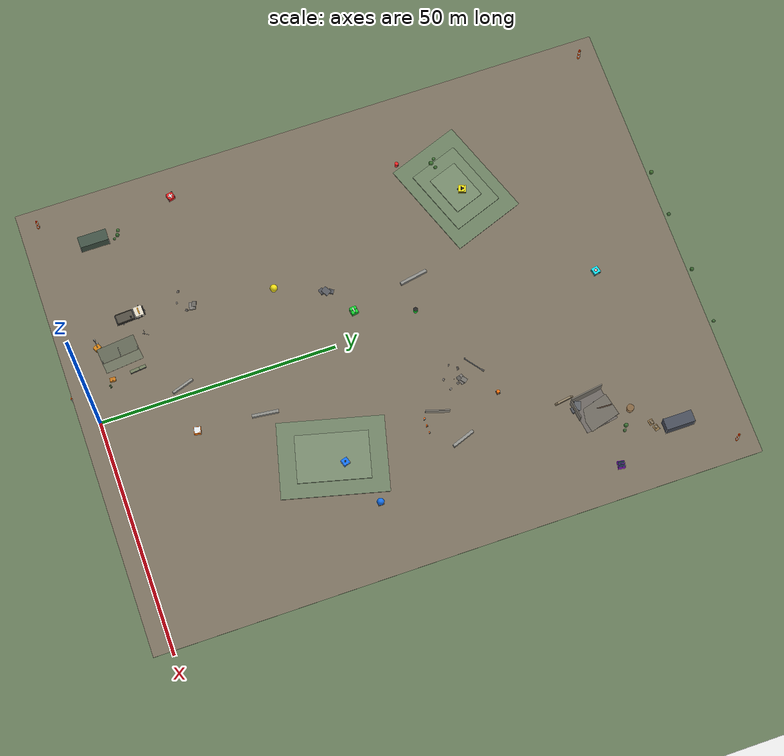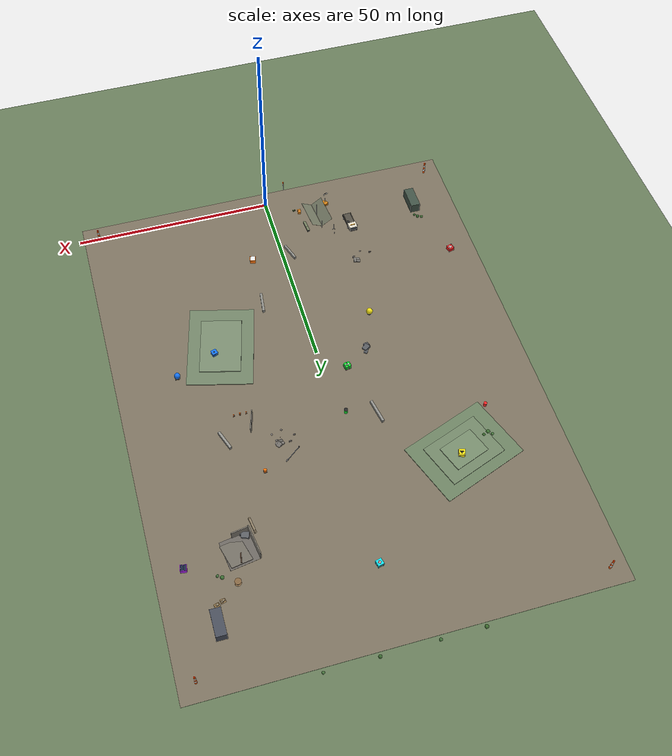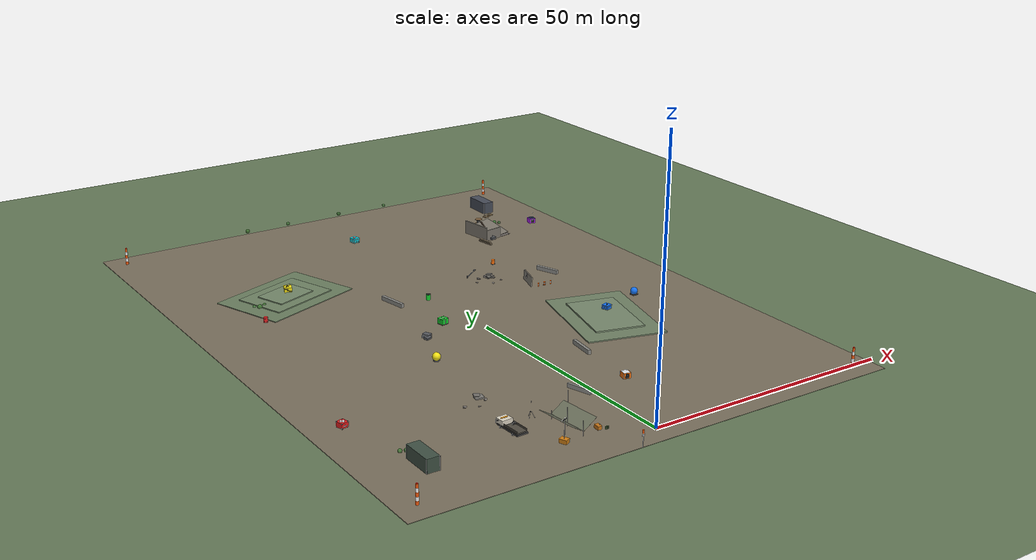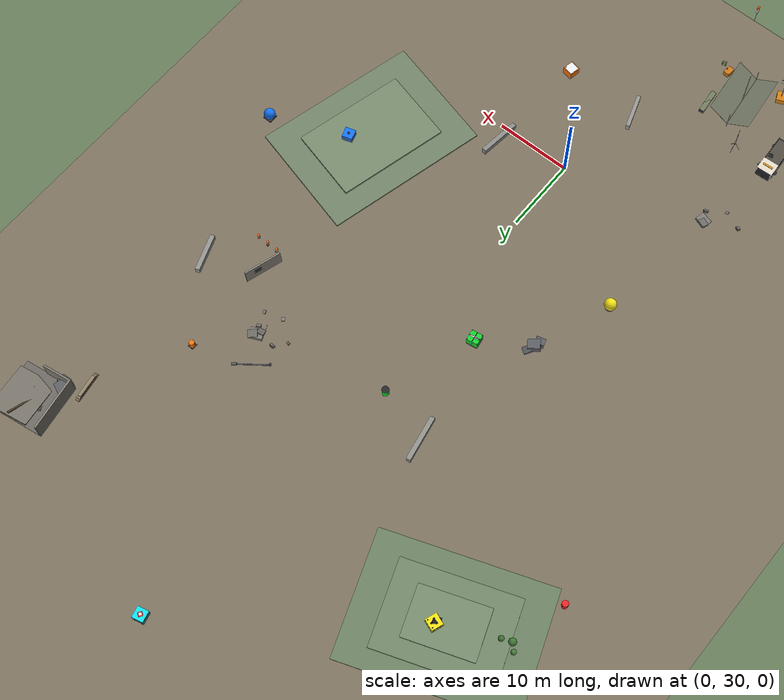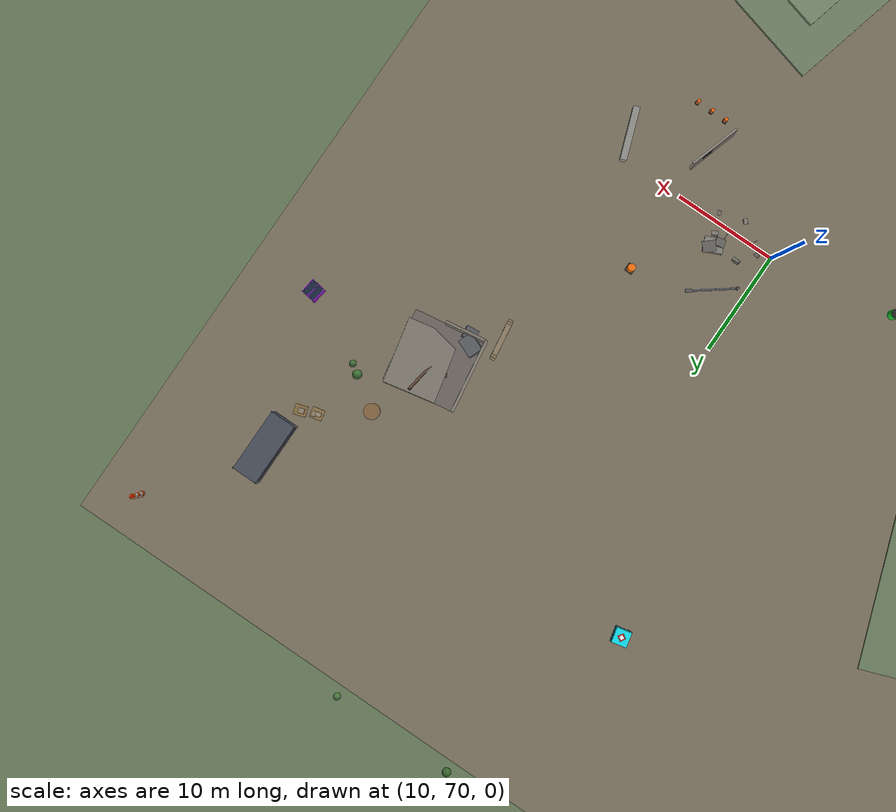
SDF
<?xml version="1.0" encoding="UTF-8"?>
<sdf version="1.9">
  <world name="box_survey">
    <physics type="ode">
      <max_step_size>0.004</max_step_size>
      <real_time_factor>1.0</real_time_factor>
      <real_time_update_rate>250</real_time_update_rate>
    </physics>
    <gravity>0 0 -9.8</gravity>
    <magnetic_field>6e-06 2.3e-05 -4.2e-05</magnetic_field>
    <atmosphere type="adiabatic"/>
    <scene>
      <grid>false</grid>
      <ambient>0.58 0.60 0.62 1</ambient>
      <background>0.70 0.82 0.94 1</background>
      <shadows>true</shadows>
    </scene>

    <!-- Global Terrain Plane: Natural Meadow Soil Surface -->
    <model name="global_terrain">
      <static>true</static>
      <link name="link">
        <collision name="collision">
          <geometry>
            <plane>
              <normal>0 0 1</normal>
              <size>1000 1000</size>
            </plane>
          </geometry>
        </collision>
        <visual name="visual">
          <geometry>
            <plane>
              <normal>0 0 1</normal>
              <size>1000 1000</size>
            </plane>
          </geometry>
          <material>
            <ambient>0.36 0.44 0.32 1</ambient>
            <diffuse>0.40 0.48 0.35 1</diffuse>
            <specular>0.04 0.04 0.04 1</specular>
          </material>
        </visual>
      </link>
      <pose>0 0 -0.01 0 0 0</pose>
    </model>

    <!-- REAL-WORLD TACTICAL SURVEY PROVING GROUND: 120m x 90m            -->
    <!-- PX4 NED: X in [0, 120]m (North), Y in [-45, 45]m (East)           -->
    <!-- Gazebo ENU: Y in [0, 120]m (North), X in [-45, 45]m (East)        -->

    <!-- Compacted Gravel Perimeter Access Road (Surrounds Survey Arena) -->
    <model name="perimeter_access_road">
      <static>true</static>
      <pose>0.0 60.0 0.001 0 0 0</pose>
      <link name="link">
        <visual name="road_surface">
          <geometry>
            <plane>
              <normal>0 0 1</normal>
              <size>98.0 128.0</size>
            </plane>
          </geometry>
          <material>
            <ambient>0.44 0.40 0.34 1</ambient>
            <diffuse>0.48 0.44 0.37 1</diffuse>
            <specular>0.02 0.02 0.02 1</specular>
          </material>
        </visual>
      </link>
    </model>

    <!-- Weathered Tarmac Survey Apron (Authentic Asphalt Proving Ground) -->
    <model name="survey_zone_apron">
      <static>true</static>
      <pose>0.0 60.0 0.002 0 0 0</pose>
      <link name="link">
        <visual name="asphalt">
          <geometry>
            <plane>
              <normal>0 0 1</normal>
              <size>90.0 120.0</size>
            </plane>
          </geometry>
          <material>
            <ambient>0.28 0.28 0.30 1</ambient>
            <diffuse>0.32 0.32 0.34 1</diffuse>
            <specular>0.08 0.08 0.08 1</specular>
          </material>
        </visual>
      </link>
    </model>

    <!-- Perimeter Survey Demarcation Markings (Ground-Painted Boundary Lines) -->
    <model name="painted_survey_perimeter">
      <static>true</static>
      <pose>0.0 60.0 0.003 0 0 0</pose>
      <link name="link">
        <!-- North line -->
        <visual name="line_n">
          <pose>0 60.0 0 0 0 0</pose>
          <geometry><box><size>90.0 0.20 0.001</size></box></geometry>
          <material><ambient>0.88 0.85 0.75 1</ambient><diffuse>0.88 0.85 0.75 1</diffuse></material>
        </visual>
        <!-- South line -->
        <visual name="line_s">
          <pose>0 -60.0 0 0 0 0</pose>
          <geometry><box><size>90.0 0.20 0.001</size></box></geometry>
          <material><ambient>0.88 0.85 0.75 1</ambient><diffuse>0.88 0.85 0.75 1</diffuse></material>
        </visual>
        <!-- East line -->
        <visual name="line_e">
          <pose>45.0 0 0 0 0 0</pose>
          <geometry><box><size>0.20 120.0 0.001</size></box></geometry>
          <material><ambient>0.88 0.85 0.75 1</ambient><diffuse>0.88 0.85 0.75 1</diffuse></material>
        </visual>
        <!-- West line -->
        <visual name="line_w">
          <pose>-45.0 0 0 0 0 0</pose>
          <geometry><box><size>0.20 120.0 0.001</size></box></geometry>
          <material><ambient>0.88 0.85 0.75 1</ambient><diffuse>0.88 0.85 0.75 1</diffuse></material>
        </visual>
      </link>
    </model>

    <!-- Photogrammetric Ground Control Points (GCP Checkered Crosses on Tarmac) -->
    <model name="gcp_markers">
      <static>true</static>
      <pose>0 0 0.004 0 0 0</pose>
      <link name="link">
        <!-- GCP 1 at (-25, 30) -->
        <visual name="gcp_1_base"><pose>-25.0 30.0 0 0 0 0</pose><geometry><box><size>1.4 1.4 0.001</size></box></geometry><material><ambient>0.9 0.9 0.9 1</ambient><diffuse>0.9 0.9 0.9 1</diffuse></material></visual>
        <visual name="gcp_1_c1"><pose>-25.35 30.35 0.001 0 0 0</pose><geometry><box><size>0.7 0.7 0.001</size></box></geometry><material><ambient>0.08 0.08 0.08 1</ambient><diffuse>0.08 0.08 0.08 1</diffuse></material></visual>
        <visual name="gcp_1_c2"><pose>-24.65 29.65 0.001 0 0 0</pose><geometry><box><size>0.7 0.7 0.001</size></box></geometry><material><ambient>0.08 0.08 0.08 1</ambient><diffuse>0.08 0.08 0.08 1</diffuse></material></visual>

        <!-- GCP 2 at (25, 30) -->
        <visual name="gcp_2_base"><pose>25.0 30.0 0 0 0 0</pose><geometry><box><size>1.4 1.4 0.001</size></box></geometry><material><ambient>0.9 0.9 0.9 1</ambient><diffuse>0.9 0.9 0.9 1</diffuse></material></visual>
        <visual name="gcp_2_c1"><pose>24.65 30.35 0.001 0 0 0</pose><geometry><box><size>0.7 0.7 0.001</size></box></geometry><material><ambient>0.08 0.08 0.08 1</ambient><diffuse>0.08 0.08 0.08 1</diffuse></material></visual>
        <visual name="gcp_2_c2"><pose>25.35 29.65 0.001 0 0 0</pose><geometry><box><size>0.7 0.7 0.001</size></box></geometry><material><ambient>0.08 0.08 0.08 1</ambient><diffuse>0.08 0.08 0.08 1</diffuse></material></visual>

        <!-- GCP 3 at (-25, 90) -->
        <visual name="gcp_3_base"><pose>-25.0 90.0 0 0 0 0</pose><geometry><box><size>1.4 1.4 0.001</size></box></geometry><material><ambient>0.9 0.9 0.9 1</ambient><diffuse>0.9 0.9 0.9 1</diffuse></material></visual>
        <visual name="gcp_3_c1"><pose>-25.35 90.35 0.001 0 0 0</pose><geometry><box><size>0.7 0.7 0.001</size></box></geometry><material><ambient>0.08 0.08 0.08 1</ambient><diffuse>0.08 0.08 0.08 1</diffuse></material></visual>
        <visual name="gcp_3_c2"><pose>-24.65 89.65 0.001 0 0 0</pose><geometry><box><size>0.7 0.7 0.001</size></box></geometry><material><ambient>0.08 0.08 0.08 1</ambient><diffuse>0.08 0.08 0.08 1</diffuse></material></visual>

        <!-- GCP 4 at (25, 90) -->
        <visual name="gcp_4_base"><pose>25.0 90.0 0 0 0 0</pose><geometry><box><size>1.4 1.4 0.001</size></box></geometry><material><ambient>0.9 0.9 0.9 1</ambient><diffuse>0.9 0.9 0.9 1</diffuse></material></visual>
        <visual name="gcp_4_c1"><pose>24.65 90.35 0.001 0 0 0</pose><geometry><box><size>0.7 0.7 0.001</size></box></geometry><material><ambient>0.08 0.08 0.08 1</ambient><diffuse>0.08 0.08 0.08 1</diffuse></material></visual>
        <visual name="gcp_4_c2"><pose>25.35 89.65 0.001 0 0 0</pose><geometry><box><size>0.7 0.7 0.001</size></box></geometry><material><ambient>0.08 0.08 0.08 1</ambient><diffuse>0.08 0.08 0.08 1</diffuse></material></visual>
      </link>
    </model>

    <!-- Realistic ICAO Aviation-Striped Survey Pylons (3.5m Towers with Red Warning Beacon) -->
    <!-- Northwest Pylon (-45, 120) -->
    <model name="survey_tower_nw">
      <static>true</static>
      <pose>-45.0 120.0 0 0 0 0</pose>
      <link name="link">
        <collision name="col"><geometry><cylinder><radius>0.35</radius><length>3.5</length></cylinder></geometry><pose>0 0 1.75 0 0 0</pose></collision>
        <visual name="b1"><pose>0 0 0.35 0 0 0</pose><geometry><cylinder><radius>0.30</radius><length>0.7</length></cylinder></geometry><material><ambient>0.95 0.35 0.05 1</ambient><diffuse>0.95 0.35 0.05 1</diffuse></material></visual>
        <visual name="b2"><pose>0 0 1.05 0 0 0</pose><geometry><cylinder><radius>0.28</radius><length>0.7</length></cylinder></geometry><material><ambient>0.95 0.95 0.95 1</ambient><diffuse>0.95 0.95 0.95 1</diffuse></material></visual>
        <visual name="b3"><pose>0 0 1.75 0 0 0</pose><geometry><cylinder><radius>0.26</radius><length>0.7</length></cylinder></geometry><material><ambient>0.95 0.35 0.05 1</ambient><diffuse>0.95 0.35 0.05 1</diffuse></material></visual>
        <visual name="b4"><pose>0 0 2.45 0 0 0</pose><geometry><cylinder><radius>0.24</radius><length>0.7</length></cylinder></geometry><material><ambient>0.95 0.95 0.95 1</ambient><diffuse>0.95 0.95 0.95 1</diffuse></material></visual>
        <visual name="b5"><pose>0 0 3.15 0 0 0</pose><geometry><cylinder><radius>0.22</radius><length>0.7</length></cylinder></geometry><material><ambient>0.95 0.35 0.05 1</ambient><diffuse>0.95 0.35 0.05 1</diffuse></material></visual>
        <visual name="beacon"><pose>0 0 3.55 0 0 0</pose><geometry><sphere><radius>0.12</radius></sphere></geometry><material><ambient>0.9 0.05 0.05 1</ambient><diffuse>0.9 0.05 0.05 1</diffuse><emissive>0.7 0.05 0.05 1</emissive></material></visual>
      </link>
    </model>

    <!-- Northeast Pylon (45, 120) -->
    <model name="survey_tower_ne">
      <static>true</static>
      <pose>45.0 120.0 0 0 0 0</pose>
      <link name="link">
        <collision name="col"><geometry><cylinder><radius>0.35</radius><length>3.5</length></cylinder></geometry><pose>0 0 1.75 0 0 0</pose></collision>
        <visual name="b1"><pose>0 0 0.35 0 0 0</pose><geometry><cylinder><radius>0.30</radius><length>0.7</length></cylinder></geometry><material><ambient>0.95 0.35 0.05 1</ambient><diffuse>0.95 0.35 0.05 1</diffuse></material></visual>
        <visual name="b2"><pose>0 0 1.05 0 0 0</pose><geometry><cylinder><radius>0.28</radius><length>0.7</length></cylinder></geometry><material><ambient>0.95 0.95 0.95 1</ambient><diffuse>0.95 0.95 0.95 1</diffuse></material></visual>
        <visual name="b3"><pose>0 0 1.75 0 0 0</pose><geometry><cylinder><radius>0.26</radius><length>0.7</length></cylinder></geometry><material><ambient>0.95 0.35 0.05 1</ambient><diffuse>0.95 0.35 0.05 1</diffuse></material></visual>
        <visual name="b4"><pose>0 0 2.45 0 0 0</pose><geometry><cylinder><radius>0.24</radius><length>0.7</length></cylinder></geometry><material><ambient>0.95 0.95 0.95 1</ambient><diffuse>0.95 0.95 0.95 1</diffuse></material></visual>
        <visual name="b5"><pose>0 0 3.15 0 0 0</pose><geometry><cylinder><radius>0.22</radius><length>0.7</length></cylinder></geometry><material><ambient>0.95 0.35 0.05 1</ambient><diffuse>0.95 0.35 0.05 1</diffuse></material></visual>
        <visual name="beacon"><pose>0 0 3.55 0 0 0</pose><geometry><sphere><radius>0.12</radius></sphere></geometry><material><ambient>0.9 0.05 0.05 1</ambient><diffuse>0.9 0.05 0.05 1</diffuse><emissive>0.7 0.05 0.05 1</emissive></material></visual>
      </link>
    </model>

    <!-- Southeast Pylon (45, 0) -->
    <model name="survey_tower_se">
      <static>true</static>
      <pose>45.0 0.0 0 0 0 0</pose>
      <link name="link">
        <collision name="col"><geometry><cylinder><radius>0.35</radius><length>3.5</length></cylinder></geometry><pose>0 0 1.75 0 0 0</pose></collision>
        <visual name="b1"><pose>0 0 0.35 0 0 0</pose><geometry><cylinder><radius>0.30</radius><length>0.7</length></cylinder></geometry><material><ambient>0.95 0.35 0.05 1</ambient><diffuse>0.95 0.35 0.05 1</diffuse></material></visual>
        <visual name="b2"><pose>0 0 1.05 0 0 0</pose><geometry><cylinder><radius>0.28</radius><length>0.7</length></cylinder></geometry><material><ambient>0.95 0.95 0.95 1</ambient><diffuse>0.95 0.95 0.95 1</diffuse></material></visual>
        <visual name="b3"><pose>0 0 1.75 0 0 0</pose><geometry><cylinder><radius>0.26</radius><length>0.7</length></cylinder></geometry><material><ambient>0.95 0.35 0.05 1</ambient><diffuse>0.95 0.35 0.05 1</diffuse></material></visual>
        <visual name="b4"><pose>0 0 2.45 0 0 0</pose><geometry><cylinder><radius>0.24</radius><length>0.7</length></cylinder></geometry><material><ambient>0.95 0.95 0.95 1</ambient><diffuse>0.95 0.95 0.95 1</diffuse></material></visual>
        <visual name="b5"><pose>0 0 3.15 0 0 0</pose><geometry><cylinder><radius>0.22</radius><length>0.7</length></cylinder></geometry><material><ambient>0.95 0.35 0.05 1</ambient><diffuse>0.95 0.35 0.05 1</diffuse></material></visual>
        <visual name="beacon"><pose>0 0 3.55 0 0 0</pose><geometry><sphere><radius>0.12</radius></sphere></geometry><material><ambient>0.9 0.05 0.05 1</ambient><diffuse>0.9 0.05 0.05 1</diffuse><emissive>0.7 0.05 0.05 1</emissive></material></visual>
      </link>
    </model>

    <!-- Southwest Pylon (-45, 0) -->
    <model name="survey_tower_sw">
      <static>true</static>
      <pose>-45.0 0.0 0 0 0 0</pose>
      <link name="link">
        <collision name="col"><geometry><cylinder><radius>0.35</radius><length>3.5</length></cylinder></geometry><pose>0 0 1.75 0 0 0</pose></collision>
        <visual name="b1"><pose>0 0 0.35 0 0 0</pose><geometry><cylinder><radius>0.30</radius><length>0.7</length></cylinder></geometry><material><ambient>0.95 0.35 0.05 1</ambient><diffuse>0.95 0.35 0.05 1</diffuse></material></visual>
        <visual name="b2"><pose>0 0 1.05 0 0 0</pose><geometry><cylinder><radius>0.28</radius><length>0.7</length></cylinder></geometry><material><ambient>0.95 0.95 0.95 1</ambient><diffuse>0.95 0.95 0.95 1</diffuse></material></visual>
        <visual name="b3"><pose>0 0 1.75 0 0 0</pose><geometry><cylinder><radius>0.26</radius><length>0.7</length></cylinder></geometry><material><ambient>0.95 0.35 0.05 1</ambient><diffuse>0.95 0.35 0.05 1</diffuse></material></visual>
        <visual name="b4"><pose>0 0 2.45 0 0 0</pose><geometry><cylinder><radius>0.24</radius><length>0.7</length></cylinder></geometry><material><ambient>0.95 0.95 0.95 1</ambient><diffuse>0.95 0.95 0.95 1</diffuse></material></visual>
        <visual name="b5"><pose>0 0 3.15 0 0 0</pose><geometry><cylinder><radius>0.22</radius><length>0.7</length></cylinder></geometry><material><ambient>0.95 0.35 0.05 1</ambient><diffuse>0.95 0.35 0.05 1</diffuse></material></visual>
        <visual name="beacon"><pose>0 0 3.55 0 0 0</pose><geometry><sphere><radius>0.12</radius></sphere></geometry><material><ambient>0.9 0.05 0.05 1</ambient><diffuse>0.9 0.05 0.05 1</diffuse><emissive>0.7 0.05 0.05 1</emissive></material></visual>
      </link>
    </model>

    <!-- Operational Helipad Launch Complex at (0, 0) -->
    <model name="helipad_complex">
      <static>true</static>
      <pose>0.0 0.0 0.003 0 0 0</pose>
      <link name="link">
        <!-- Octagonal landing pad border -->
        <visual name="pad_surface">
          <geometry><cylinder><radius>4.0</radius><length>0.005</length></cylinder></geometry>
          <material><ambient>0.22 0.24 0.28 1</ambient><diffuse>0.25 0.28 0.32 1</diffuse></material>
        </visual>
        <!-- White Ring Marking -->
        <visual name="white_ring">
          <pose>0 0 0.003 0 0 0</pose>
          <geometry><cylinder><radius>3.2</radius><length>0.002</length></cylinder></geometry>
          <material><ambient>0.92 0.92 0.92 1</ambient><diffuse>0.92 0.92 0.92 1</diffuse></material>
        </visual>
        <visual name="inner_pad">
          <pose>0 0 0.004 0 0 0</pose>
          <geometry><cylinder><radius>2.9</radius><length>0.002</length></cylinder></geometry>
          <material><ambient>0.22 0.24 0.28 1</ambient><diffuse>0.25 0.28 0.32 1</diffuse></material>
        </visual>
        <!-- Bold White "H" Marking -->
        <visual name="h_bar_left"><pose>-0.6 0 0.005 0 0 0</pose><geometry><box><size>0.28 1.6 0.002</size></box></geometry><material><ambient>0.95 0.95 0.95 1</ambient><diffuse>0.95 0.95 0.95 1</diffuse></material></visual>
        <visual name="h_bar_right"><pose>0.6 0 0.005 0 0 0</pose><geometry><box><size>0.28 1.6 0.002</size></box></geometry><material><ambient>0.95 0.95 0.95 1</ambient><diffuse>0.95 0.95 0.95 1</diffuse></material></visual>
        <visual name="h_bar_cross"><pose>0 0 0.005 0 0 0</pose><geometry><box><size>1.2 0.28 0.002</size></box></geometry><material><ambient>0.95 0.95 0.95 1</ambient><diffuse>0.95 0.95 0.95 1</diffuse></material></visual>
      </link>
    </model>

    <!-- Field Weather Station & Anemometer Mast near Launch Pad -->
    <model name="weather_mast">
      <static>true</static>
      <pose>-6.0 -4.0 0 0 0 0</pose>
      <link name="link">
        <collision name="col"><geometry><cylinder><radius>0.08</radius><length>2.8</length></cylinder></geometry><pose>0 0 1.4 0 0 0</pose></collision>
        <visual name="pole"><pose>0 0 1.4 0 0 0</pose><geometry><cylinder><radius>0.05</radius><length>2.8</length></cylinder></geometry><material><ambient>0.75 0.78 0.82 1</ambient><diffuse>0.75 0.78 0.82 1</diffuse></material></visual>
        <visual name="sensor_box"><pose>0 0 2.2 0 0 0</pose><geometry><box><size>0.3 0.25 0.4</size></box></geometry><material><ambient>0.85 0.85 0.85 1</ambient><diffuse>0.85 0.85 0.85 1</diffuse></material></visual>
        <visual name="wind_sock"><pose>0 0 2.8 0 0 0</pose><geometry><cylinder><radius>0.15</radius><length>0.6</length></cylinder></geometry><material><ambient>0.95 0.35 0.05 1</ambient><diffuse>0.95 0.35 0.05 1</diffuse></material></visual>
      </link>
    </model>

    <!-- REALISTIC NATURAL TERRAIN: CONTOURED HILLS, BERMS & BOULDERS     -->

    <!-- Natural Rolling Knoll (North-West Terraced Contoured Elevation +0.6m) -->
    <model name="natural_knoll_nw">
      <static>true</static>
      <pose>-25.0 85.0 0 0 0 0.35</pose>
      <link name="link">
        <!-- Tier 1: Gentle Base Slope (+0.22m) -->
        <collision name="col_t1"><pose>0 0 0.11 0 0 0</pose><geometry><box><size>22.0 16.0 0.22</size></box></geometry></collision>
        <visual name="vis_t1"><pose>0 0 0.11 0 0 0</pose><geometry><box><size>22.0 16.0 0.22</size></box></geometry><material><ambient>0.38 0.46 0.34 1</ambient><diffuse>0.42 0.50 0.38 1</diffuse></material></visual>
        <!-- Tier 2: Mid Elevation (+0.44m) -->
        <collision name="col_t2"><pose>0 0 0.33 0 0 0</pose><geometry><box><size>15.0 11.0 0.22</size></box></geometry></collision>
        <visual name="vis_t2"><pose>0 0 0.33 0 0 0</pose><geometry><box><size>15.0 11.0 0.22</size></box></geometry><material><ambient>0.40 0.48 0.36 1</ambient><diffuse>0.44 0.52 0.40 1</diffuse></material></visual>
        <!-- Tier 3: Summit Crest (+0.65m) -->
        <collision name="col_t3"><pose>0 0 0.55 0 0 0</pose><geometry><box><size>9.0 6.5 0.22</size></box></geometry></collision>
        <visual name="vis_t3"><pose>0 0 0.55 0 0 0</pose><geometry><box><size>9.0 6.5 0.22</size></box></geometry><material><ambient>0.42 0.50 0.38 1</ambient><diffuse>0.46 0.54 0.42 1</diffuse></material></visual>
      </link>
    </model>

    <!-- Natural Ridge (Central-East Elongated Elevation +0.7m) -->
    <model name="natural_ridge_ce">
      <static>true</static>
      <pose>22.0 42.0 0 0 0 -0.25</pose>
      <link name="link">
        <!-- Base Ridge Tier (+0.30m) -->
        <collision name="col_r1"><pose>0 0 0.15 0 0 0</pose><geometry><box><size>16.0 22.0 0.30</size></box></geometry></collision>
        <visual name="vis_r1"><pose>0 0 0.15 0 0 0</pose><geometry><box><size>16.0 22.0 0.30</size></box></geometry><material><ambient>0.40 0.47 0.36 1</ambient><diffuse>0.44 0.51 0.40 1</diffuse></material></visual>
        <!-- Spine Ridge Tier (+0.68m) -->
        <collision name="col_r2"><pose>0 0 0.45 0 0 0</pose><geometry><box><size>10.0 15.0 0.30</size></box></geometry></collision>
        <visual name="vis_r2"><pose>0 0 0.45 0 0 0</pose><geometry><box><size>10.0 15.0 0.30</size></box></geometry><material><ambient>0.43 0.50 0.39 1</ambient><diffuse>0.47 0.54 0.43 1</diffuse></material></visual>
      </link>
    </model>

    <!-- Natural Rocky Outcrop Clusters (Irregular Multi-Stone Formations) -->
    <model name="rock_outcrop_alpha">
      <static>true</static>
      <pose>-12.0 52.0 0 0 0 0.6</pose>
      <link name="link">
        <collision name="c1"><pose>0 0 0.4 0 0 0</pose><geometry><box><size>1.6 1.3 0.8</size></box></geometry></collision>
        <visual name="v1"><pose>0 0 0.4 0.1 0.15 0</pose><geometry><box><size>1.6 1.3 0.8</size></box></geometry><material><ambient>0.32 0.33 0.35 1</ambient><diffuse>0.36 0.37 0.39 1</diffuse></material></visual>
        <visual name="v2"><pose>0.8 0.6 0.25 -0.1 0.2 0.4</pose><geometry><box><size>1.1 0.9 0.5</size></box></geometry><material><ambient>0.28 0.29 0.31 1</ambient><diffuse>0.32 0.33 0.35 1</diffuse></material></visual>
        <visual name="v3"><pose>-0.7 -0.5 0.3 0.2 -0.1 -0.3</pose><geometry><box><size>1.2 1.0 0.6</size></box></geometry><material><ambient>0.30 0.31 0.33 1</ambient><diffuse>0.34 0.35 0.37 1</diffuse></material></visual>
      </link>
    </model>

    <model name="rock_outcrop_beta">
      <static>true</static>
      <pose>28.0 92.0 0 0 0 -0.4</pose>
      <link name="link">
        <collision name="c1"><pose>0 0 0.5 0 0 0</pose><geometry><box><size>1.8 1.4 1.0</size></box></geometry></collision>
        <visual name="v1"><pose>0 0 0.5 -0.15 0.1 0</pose><geometry><box><size>1.8 1.4 1.0</size></box></geometry><material><ambient>0.33 0.34 0.36 1</ambient><diffuse>0.37 0.38 0.40 1</diffuse></material></visual>
        <visual name="v2"><pose>0.9 -0.5 0.35 0.15 -0.1 0.5</pose><geometry><box><size>1.2 1.1 0.7</size></box></geometry><material><ambient>0.29 0.30 0.32 1</ambient><diffuse>0.33 0.34 0.36 1</diffuse></material></visual>
      </link>
    </model>

    <!-- Concrete Jersey Barriers Between Flight Lanes -->
    <model name="jersey_barrier_1">
      <static>true</static>
      <pose>-9.0 70.0 0 0 0 0.18</pose>
      <link name="link">
        <collision name="col"><pose>0 0 0.45 0 0 0</pose><geometry><box><size>0.6 6.0 0.9</size></box></geometry></collision>
        <visual name="vis"><pose>0 0 0.45 0 0 0</pose><geometry><box><size>0.6 6.0 0.9</size></box></geometry><material><ambient>0.52 0.52 0.50 1</ambient><diffuse>0.56 0.56 0.54 1</diffuse></material></visual>
      </link>
    </model>

    <model name="jersey_barrier_2">
      <static>true</static>
      <pose>9.0 32.0 0 0 0 -0.12</pose>
      <link name="link">
        <collision name="col"><pose>0 0 0.45 0 0 0</pose><geometry><box><size>0.6 5.5 0.9</size></box></geometry></collision>
        <visual name="vis"><pose>0 0 0.45 0 0 0</pose><geometry><box><size>0.6 5.5 0.9</size></box></geometry><material><ambient>0.50 0.50 0.48 1</ambient><diffuse>0.54 0.54 0.52 1</diffuse></material></visual>
      </link>
    </model>

    <model name="jersey_barrier_3">
      <static>true</static>
      <pose>27.0 68.0 0 0 0 0.35</pose>
      <link name="link">
        <collision name="col"><pose>0 0 0.45 0 0 0</pose><geometry><box><size>0.6 5.0 0.9</size></box></geometry></collision>
        <visual name="vis"><pose>0 0 0.45 0 0 0</pose><geometry><box><size>0.6 5.0 0.9</size></box></geometry><material><ambient>0.53 0.53 0.51 1</ambient><diffuse>0.57 0.57 0.55 1</diffuse></material></visual>
      </link>
    </model>

    <!-- CRITICAL INFRASTRUCTURE: ISO CONTAINERS & DISASTER RUBBLE        -->
    <!-- Adds realistic vertical scale, optical shadows & occlusions      -->

    <!-- Staging Compound ISO Shipping Container 1 (West Perimeter Access) -->
    <model name="iso_container_west">
      <static>true</static>
      <pose>-38.0 10.0 0 0 0 0</pose>
      <link name="link">
        <collision name="col"><pose>0 0 1.3 0 0 0</pose><geometry><box><size>2.44 6.06 2.60</size></box></geometry></collision>
        <visual name="body"><pose>0 0 1.3 0 0 0</pose><geometry><box><size>2.44 6.06 2.60</size></box></geometry><material><ambient>0.22 0.28 0.24 1</ambient><diffuse>0.25 0.32 0.27 1</diffuse><specular>0.1 0.1 0.1 1</specular></material></visual>
        <visual name="corner_post_1"><pose>-1.20 -3.00 1.3 0 0 0</pose><geometry><box><size>0.12 0.12 2.60</size></box></geometry><material><ambient>0.12 0.12 0.12 1</ambient><diffuse>0.12 0.12 0.12 1</diffuse></material></visual>
        <visual name="corner_post_2"><pose>1.20 -3.00 1.3 0 0 0</pose><geometry><box><size>0.12 0.12 2.60</size></box></geometry><material><ambient>0.12 0.12 0.12 1</ambient><diffuse>0.12 0.12 0.12 1</diffuse></material></visual>
        <visual name="corner_post_3"><pose>-1.20 3.00 1.3 0 0 0</pose><geometry><box><size>0.12 0.12 2.60</size></box></geometry><material><ambient>0.12 0.12 0.12 1</ambient><diffuse>0.12 0.12 0.12 1</diffuse></material></visual>
        <visual name="corner_post_4"><pose>1.20 3.00 1.3 0 0 0</pose><geometry><box><size>0.12 0.12 2.60</size></box></geometry><material><ambient>0.12 0.12 0.12 1</ambient><diffuse>0.12 0.12 0.12 1</diffuse></material></visual>
      </link>
    </model>

    <!-- Staging Compound ISO Shipping Container 2 (East Perimeter Compound) -->
    <model name="iso_container_east">
      <static>true</static>
      <pose>38.0 110.0 0 0 0 0</pose>
      <link name="link">
        <collision name="col"><pose>0 0 1.3 0 0 0</pose><geometry><box><size>2.44 6.06 2.60</size></box></geometry></collision>
        <visual name="body"><pose>0 0 1.3 0 0 0</pose><geometry><box><size>2.44 6.06 2.60</size></box></geometry><material><ambient>0.24 0.26 0.30 1</ambient><diffuse>0.28 0.30 0.35 1</diffuse><specular>0.1 0.1 0.1 1</specular></material></visual>
        <visual name="corner_post_1"><pose>-1.20 -3.00 1.3 0 0 0</pose><geometry><box><size>0.12 0.12 2.60</size></box></geometry><material><ambient>0.12 0.12 0.12 1</ambient><diffuse>0.12 0.12 0.12 1</diffuse></material></visual>
        <visual name="corner_post_2"><pose>1.20 -3.00 1.3 0 0 0</pose><geometry><box><size>0.12 0.12 2.60</size></box></geometry><material><ambient>0.12 0.12 0.12 1</ambient><diffuse>0.12 0.12 0.12 1</diffuse></material></visual>
        <visual name="corner_post_3"><pose>-1.20 3.00 1.3 0 0 0</pose><geometry><box><size>0.12 0.12 2.60</size></box></geometry><material><ambient>0.12 0.12 0.12 1</ambient><diffuse>0.12 0.12 0.12 1</diffuse></material></visual>
        <visual name="corner_post_4"><pose>1.20 3.00 1.3 0 0 0</pose><geometry><box><size>0.12 0.12 2.60</size></box></geometry><material><ambient>0.12 0.12 0.12 1</ambient><diffuse>0.12 0.12 0.12 1</diffuse></material></visual>
      </link>
    </model>

    <!-- Disaster Rubble & Masonry Collapse Piles -->
    <model name="rubble_debris_cluster_1">
      <static>true</static>
      <pose>15.0 72.0 0 0 0 0.4</pose>
      <link name="link">
        <collision name="col"><pose>0 0 0.35 0 0 0</pose><geometry><box><size>2.2 1.8 0.7</size></box></geometry></collision>
        <visual name="slab1"><pose>0 0 0.2 0.1 0.05 0</pose><geometry><box><size>1.8 1.4 0.4</size></box></geometry><material><ambient>0.45 0.44 0.42 1</ambient><diffuse>0.50 0.48 0.46 1</diffuse></material></visual>
        <visual name="slab2"><pose>0.4 0.2 0.45 -0.1 0.15 0.3</pose><geometry><box><size>1.2 1.0 0.3</size></box></geometry><material><ambient>0.40 0.39 0.37 1</ambient><diffuse>0.44 0.43 0.41 1</diffuse></material></visual>
        <visual name="stone"><pose>-0.5 -0.3 0.25 0.2 -0.1 -0.2</pose><geometry><box><size>0.9 0.8 0.5</size></box></geometry><material><ambient>0.35 0.34 0.32 1</ambient><diffuse>0.38 0.37 0.35 1</diffuse></material></visual>
      </link>
    </model>

    <model name="rubble_debris_cluster_2">
      <static>true</static>
      <pose>-18.0 25.0 0 0 0 -0.2</pose>
      <link name="link">
        <collision name="col"><pose>0 0 0.3 0 0 0</pose><geometry><box><size>2.0 1.6 0.6</size></box></geometry></collision>
        <visual name="slab1"><pose>0 0 0.18 0.05 -0.1 0</pose><geometry><box><size>1.6 1.3 0.35</size></box></geometry><material><ambient>0.44 0.43 0.41 1</ambient><diffuse>0.48 0.47 0.45 1</diffuse></material></visual>
        <visual name="slab2"><pose>-0.3 0.4 0.4 0.15 0.05 -0.2</pose><geometry><box><size>1.1 0.9 0.3</size></box></geometry><material><ambient>0.38 0.37 0.35 1</ambient><diffuse>0.42 0.41 0.39 1</diffuse></material></visual>
      </link>
    </model>

    <!-- 7 HIGH-FIDELITY TARGET CARGO CUBES DISPERSED IN ARENA            -->
    <!-- Testing Edge-of-View, Lateral Flanks, Boundaries & Terrain       -->
    <!-- Gazebo ENU: X_gz = Y_ned (East), Y_gz = X_ned (North)            -->

    <!-- TARGET 1: TRAUMA MEDICAL CACHE [RED] - Far-West Perimeter Edge (X_ned=28.0, Y_ned=-42.5) -->
    <!-- Military field surgical & trauma care equipment chest with cross emblem & drop handles -->
    <model name="target_cube_red">
      <static>true</static>
      <pose>-42.5 28.0 0 0 0 0.25</pose>
      <link name="link">
        <collision name="col"><pose>0 0 0.6 0 0 0</pose><geometry><box><size>1.5 1.5 1.2</size></box></geometry></collision>
        <!-- Heavy Pallet Base Skids -->
        <visual name="skid_left"><pose>-0.55 0 0.06 0 0 0</pose><geometry><box><size>0.16 1.50 0.12</size></box></geometry><material><ambient>0.12 0.12 0.12 1</ambient><diffuse>0.14 0.14 0.14 1</diffuse></material></visual>
        <visual name="skid_right"><pose>0.55 0 0.06 0 0 0</pose><geometry><box><size>0.16 1.50 0.12</size></box></geometry><material><ambient>0.12 0.12 0.12 1</ambient><diffuse>0.14 0.14 0.14 1</diffuse></material></visual>
        <!-- Main Red Medical Chest Body -->
        <visual name="body"><pose>0 0 0.60 0 0 0</pose><geometry><box><size>1.46 1.46 0.96</size></box></geometry><material><ambient>0.88 0.10 0.10 1</ambient><diffuse>0.92 0.12 0.12 1</diffuse><specular>0.3 0.3 0.3 1</specular></material></visual>
        <!-- Black Protective Corner Armor Caps (8 corners) -->
        <visual name="cap_blf"><pose>-0.65 -0.65 0.20 0 0 0</pose><geometry><box><size>0.20 0.20 0.22</size></box></geometry><material><ambient>0.10 0.10 0.10 1</ambient><diffuse>0.12 0.12 0.12 1</diffuse></material></visual>
        <visual name="cap_brf"><pose>0.65 -0.65 0.20 0 0 0</pose><geometry><box><size>0.20 0.20 0.22</size></box></geometry><material><ambient>0.10 0.10 0.10 1</ambient><diffuse>0.12 0.12 0.12 1</diffuse></material></visual>
        <visual name="cap_blr"><pose>-0.65 0.65 0.20 0 0 0</pose><geometry><box><size>0.20 0.20 0.22</size></box></geometry><material><ambient>0.10 0.10 0.10 1</ambient><diffuse>0.12 0.12 0.12 1</diffuse></material></visual>
        <visual name="cap_brr"><pose>0.65 0.65 0.20 0 0 0</pose><geometry><box><size>0.20 0.20 0.22</size></box></geometry><material><ambient>0.10 0.10 0.10 1</ambient><diffuse>0.12 0.12 0.12 1</diffuse></material></visual>
        <visual name="cap_tlf"><pose>-0.65 -0.65 1.00 0 0 0</pose><geometry><box><size>0.20 0.20 0.20</size></box></geometry><material><ambient>0.10 0.10 0.10 1</ambient><diffuse>0.12 0.12 0.12 1</diffuse></material></visual>
        <visual name="cap_trf"><pose>0.65 -0.65 1.00 0 0 0</pose><geometry><box><size>0.20 0.20 0.20</size></box></geometry><material><ambient>0.10 0.10 0.10 1</ambient><diffuse>0.12 0.12 0.12 1</diffuse></material></visual>
        <visual name="cap_tlr"><pose>-0.65 0.65 1.00 0 0 0</pose><geometry><box><size>0.20 0.20 0.20</size></box></geometry><material><ambient>0.10 0.10 0.10 1</ambient><diffuse>0.12 0.12 0.12 1</diffuse></material></visual>
        <visual name="cap_trr"><pose>0.65 0.65 1.00 0 0 0</pose><geometry><box><size>0.20 0.20 0.20</size></box></geometry><material><ambient>0.10 0.10 0.10 1</ambient><diffuse>0.12 0.12 0.12 1</diffuse></material></visual>
        <!-- Prominent White Medical Cross on Top Lid -->
        <visual name="cross_v"><pose>0 0 1.085 0 0 0</pose><geometry><box><size>0.34 0.98 0.02</size></box></geometry><material><ambient>0.95 0.95 0.95 1</ambient><diffuse>0.98 0.98 0.98 1</diffuse></material></visual>
        <visual name="cross_h"><pose>0 0 1.085 0 0 0</pose><geometry><box><size>0.98 0.34 0.02</size></box></geometry><material><ambient>0.95 0.95 0.95 1</ambient><diffuse>0.98 0.98 0.98 1</diffuse></material></visual>
        <!-- Heavy Drop Handles & Hardware -->
        <visual name="handle_f"><pose>0 -0.74 0.65 0 0 0</pose><geometry><box><size>0.28 0.04 0.08</size></box></geometry><material><ambient>0.12 0.12 0.12 1</ambient><diffuse>0.14 0.14 0.14 1</diffuse></material></visual>
        <visual name="handle_r"><pose>0 0.74 0.65 0 0 0</pose><geometry><box><size>0.28 0.04 0.08</size></box></geometry><material><ambient>0.12 0.12 0.12 1</ambient><diffuse>0.14 0.14 0.14 1</diffuse></material></visual>
        <!-- White Stenciled Triage Identification Plate on Front -->
        <visual name="id_plate"><pose>0 -0.735 0.45 0 0 0</pose><geometry><box><size>0.65 0.01 0.16</size></box></geometry><material><ambient>0.92 0.92 0.92 1</ambient><diffuse>0.95 0.95 0.95 1</diffuse></material></visual>
        <!-- Pressure Equalization Relief Valve on Top -->
        <visual name="valve"><pose>0.48 0.48 1.09 0 0 0</pose><geometry><cylinder><radius>0.06</radius><length>0.04</length></cylinder></geometry><material><ambient>0.15 0.15 0.15 1</ambient><diffuse>0.20 0.20 0.20 1</diffuse></material></visual>
      </link>
    </model>

    <!-- TARGET 2: HAZMAT TOXIC SPILL OVERPACK [YELLOW] - NW Knoll Tier 2 Summit (X_ned=86.0, Y_ned=-24.0, Z_ned=-0.44m) -->
    <!-- Hazardous chemical containment unit with secondary containment sump pallet & biohazard emblem -->
    <model name="target_cube_yellow">
      <static>true</static>
      <pose>-24.0 86.0 0.44 0 0 -0.35</pose>
      <link name="link">
        <collision name="col"><pose>0 0 0.65 0 0 0</pose><geometry><box><size>1.6 1.6 1.3</size></box></geometry></collision>
        <!-- Heavy Black Secondary Spill Containment Sump Pallet -->
        <visual name="sump_tray"><pose>0 0 0.08 0 0 0</pose><geometry><box><size>1.70 1.70 0.16</size></box></geometry><material><ambient>0.10 0.10 0.10 1</ambient><diffuse>0.12 0.12 0.12 1</diffuse></material></visual>
        <visual name="sump_drain"><pose>0.82 0 0.08 0 1.5708 0</pose><geometry><cylinder><radius>0.04</radius><length>0.08</length></cylinder></geometry><material><ambient>0.3 0.3 0.3 1</ambient><diffuse>0.35 0.35 0.35 1</diffuse></material></visual>
        <!-- Main Yellow Chemical Containment Chest Body -->
        <visual name="body"><pose>0 0 0.68 0 0 0</pose><geometry><box><size>1.52 1.52 1.08</size></box></geometry><material><ambient>0.92 0.85 0.06 1</ambient><diffuse>0.95 0.88 0.08 1</diffuse><specular>0.3 0.3 0.3 1</specular></material></visual>
        <!-- Black Tension Bands Clamping Vault -->
        <visual name="band_lower"><pose>0 0 0.42 0 0 0</pose><geometry><box><size>1.55 1.55 0.06</size></box></geometry><material><ambient>0.12 0.12 0.12 1</ambient><diffuse>0.14 0.14 0.14 1</diffuse></material></visual>
        <visual name="band_upper"><pose>0 0 0.90 0 0 0</pose><geometry><box><size>1.55 1.55 0.06</size></box></geometry><material><ambient>0.12 0.12 0.12 1</ambient><diffuse>0.14 0.14 0.14 1</diffuse></material></visual>
        <!-- Biohazard / Hazard Warning Emblem on Top Lid -->
        <visual name="bio_disk"><pose>0 0 1.225 0 0 0</pose><geometry><cylinder><radius>0.24</radius><length>0.02</length></cylinder></geometry><material><ambient>0.08 0.08 0.08 1</ambient><diffuse>0.10 0.10 0.10 1</diffuse></material></visual>
        <visual name="bio_petal1"><pose>0 0.32 1.225 0 0 0</pose><geometry><cylinder><radius>0.14</radius><length>0.02</length></cylinder></geometry><material><ambient>0.08 0.08 0.08 1</ambient><diffuse>0.10 0.10 0.10 1</diffuse></material></visual>
        <visual name="bio_petal2"><pose>-0.28 -0.16 1.225 0 0 0</pose><geometry><cylinder><radius>0.14</radius><length>0.02</length></cylinder></geometry><material><ambient>0.08 0.08 0.08 1</ambient><diffuse>0.10 0.10 0.10 1</diffuse></material></visual>
        <visual name="bio_petal3"><pose>0.28 -0.16 1.225 0 0 0</pose><geometry><cylinder><radius>0.14</radius><length>0.02</length></cylinder></geometry><material><ambient>0.08 0.08 0.08 1</ambient><diffuse>0.10 0.10 0.10 1</diffuse></material></visual>
        <!-- Chemical Vapor Exhaust Vents on Top -->
        <visual name="vent_1"><pose>-0.52 0.52 1.27 0 0 0</pose><geometry><cylinder><radius>0.07</radius><length>0.12</length></cylinder></geometry><material><ambient>0.20 0.20 0.20 1</ambient><diffuse>0.25 0.25 0.25 1</diffuse></material></visual>
        <visual name="vent_2"><pose>0.52 0.52 1.27 0 0 0</pose><geometry><cylinder><radius>0.07</radius><length>0.12</length></cylinder></geometry><material><ambient>0.20 0.20 0.20 1</ambient><diffuse>0.25 0.25 0.25 1</diffuse></material></visual>
        <!-- Hazmat Warning Diamond Placard on Front -->
        <visual name="diamond_placard"><pose>0 -0.765 0.65 0 0 0.7854</pose><geometry><box><size>0.42 0.42 0.01</size></box></geometry><material><ambient>0.08 0.08 0.08 1</ambient><diffuse>0.10 0.10 0.10 1</diffuse></material></visual>
      </link>
    </model>

    <!-- TARGET 3: EMERGENCY RATIONS POD [GREEN] - Inter-Swath Flank (X_ned=56.0, Y_ned=-6.0) -->
    <!-- Humanitarian emergency provisions pod with heavy cargo webbing, lifting lugs & UN markings -->
    <model name="target_cube_green">
      <static>true</static>
      <pose>-6.0 56.0 0 0 0 0.15</pose>
      <link name="link">
        <collision name="col"><pose>0 0 0.65 0 0 0</pose><geometry><box><size>1.6 1.5 1.3</size></box></geometry></collision>
        <!-- Heavy Composite Pallet Foundation with Forklift Channels -->
        <visual name="pallet_base"><pose>0 0 0.06 0 0 0</pose><geometry><box><size>1.56 1.50 0.12</size></box></geometry><material><ambient>0.22 0.20 0.18 1</ambient><diffuse>0.28 0.25 0.22 1</diffuse></material></visual>
        <!-- Main Olive Green Provisions Pod Body -->
        <visual name="body"><pose>0 0 0.68 0 0 0</pose><geometry><box><size>1.50 1.44 1.06</size></box></geometry><material><ambient>0.06 0.78 0.16 1</ambient><diffuse>0.08 0.82 0.18 1</diffuse><specular>0.3 0.3 0.3 1</specular></material></visual>
        <!-- Heavy Black Cargo Ratchet Straps Crossing Top & Sides -->
        <visual name="strap_long"><pose>0 0 0.68 0 0 0</pose><geometry><box><size>1.52 0.08 1.08</size></box></geometry><material><ambient>0.08 0.08 0.08 1</ambient><diffuse>0.10 0.10 0.10 1</diffuse></material></visual>
        <visual name="strap_lat"><pose>0 0 0.68 0 0 0</pose><geometry><box><size>0.08 1.46 1.08</size></box></geometry><material><ambient>0.08 0.08 0.08 1</ambient><diffuse>0.10 0.10 0.10 1</diffuse></material></visual>
        <!-- Helicopter Crane Lifting Eyes (4 corners) -->
        <visual name="lift_fl"><pose>-0.68 -0.65 1.25 0 0 0</pose><geometry><cylinder><radius>0.05</radius><length>0.08</length></cylinder></geometry><material><ambient>0.15 0.15 0.15 1</ambient><diffuse>0.20 0.20 0.20 1</diffuse></material></visual>
        <visual name="lift_fr"><pose>0.68 -0.65 1.25 0 0 0</pose><geometry><cylinder><radius>0.05</radius><length>0.08</length></cylinder></geometry><material><ambient>0.15 0.15 0.15 1</ambient><diffuse>0.20 0.20 0.20 1</diffuse></material></visual>
        <visual name="lift_rl"><pose>-0.68 0.65 1.25 0 0 0</pose><geometry><cylinder><radius>0.05</radius><length>0.08</length></cylinder></geometry><material><ambient>0.15 0.15 0.15 1</ambient><diffuse>0.20 0.20 0.20 1</diffuse></material></visual>
        <visual name="lift_rr"><pose>0.68 0.65 1.25 0 0 0</pose><geometry><cylinder><radius>0.05</radius><length>0.08</length></cylinder></geometry><material><ambient>0.15 0.15 0.15 1</ambient><diffuse>0.20 0.20 0.20 1</diffuse></material></visual>
        <!-- White Humanitarian Relief Aid Stencil Stripe on Top -->
        <visual name="stencil_stripe"><pose>0 0 1.215 0 0 0</pose><geometry><box><size>1.05 0.26 0.01</size></box></geometry><material><ambient>0.92 0.92 0.92 1</ambient><diffuse>0.96 0.96 0.96 1</diffuse></material></visual>
        <!-- Front Dual Recessed Twist Latches -->
        <visual name="latch_1"><pose>-0.40 -0.725 0.70 0 0 0</pose><geometry><box><size>0.12 0.02 0.10</size></box></geometry><material><ambient>0.10 0.10 0.10 1</ambient><diffuse>0.12 0.12 0.12 1</diffuse></material></visual>
        <visual name="latch_2"><pose>0.40 -0.725 0.70 0 0 0</pose><geometry><box><size>0.12 0.02 0.10</size></box></geometry><material><ambient>0.10 0.10 0.10 1</ambient><diffuse>0.12 0.12 0.12 1</diffuse></material></visual>
      </link>
    </model>

    <!-- TARGET 4: SURVIVOR SHELTER [ORANGE] - Southern Sector Approach (X_ned=18.0, Y_ned=8.0) -->
    <!-- Rapid-deployment insulated thermal survival pod with reflective roof, entrance flap & strobe beacon -->
    <model name="target_cube_orange">
      <static>true</static>
      <pose>8.0 18.0 0 0 0 -0.2</pose>
      <link name="link">
        <collision name="col"><pose>0 0 0.6 0 0 0</pose><geometry><box><size>1.5 1.5 1.2</size></box></geometry></collision>
        <!-- Base Skid Foundation -->
        <visual name="skid_l"><pose>-0.55 0 0.05 0 0 0</pose><geometry><box><size>0.16 1.46 0.10</size></box></geometry><material><ambient>0.15 0.15 0.15 1</ambient><diffuse>0.15 0.15 0.15 1</diffuse></material></visual>
        <visual name="skid_r"><pose>0.55 0 0.05 0 0 0</pose><geometry><box><size>0.16 1.46 0.10</size></box></geometry><material><ambient>0.15 0.15 0.15 1</ambient><diffuse>0.15 0.15 0.15 1</diffuse></material></visual>
        <!-- Main Safety Orange Survival Pod Body -->
        <visual name="body"><pose>0 0 0.62 0 0 0</pose><geometry><box><size>1.46 1.46 1.04</size></box></geometry><material><ambient>0.95 0.42 0.04 1</ambient><diffuse>0.98 0.45 0.05 1</diffuse><specular>0.3 0.3 0.3 1</specular></material></visual>
        <!-- Reflective Silver Thermal Roof Insulation Cap -->
        <visual name="thermal_roof"><pose>0 0 1.15 0 0 0</pose><geometry><box><size>1.30 1.30 0.04</size></box></geometry><material><ambient>0.85 0.88 0.90 1</ambient><diffuse>0.90 0.92 0.94 1</diffuse><specular>0.5 0.5 0.5 1</specular></material></visual>
        <!-- Black Exoskeleton Structural Corner Ribs -->
        <visual name="rib_fl"><pose>-0.70 -0.70 0.62 0 0 0</pose><geometry><cylinder><radius>0.04</radius><length>1.04</length></cylinder></geometry><material><ambient>0.10 0.10 0.10 1</ambient><diffuse>0.12 0.12 0.12 1</diffuse></material></visual>
        <visual name="rib_fr"><pose>0.70 -0.70 0.62 0 0 0</pose><geometry><cylinder><radius>0.04</radius><length>1.04</length></cylinder></geometry><material><ambient>0.10 0.10 0.10 1</ambient><diffuse>0.12 0.12 0.12 1</diffuse></material></visual>
        <visual name="rib_rl"><pose>-0.70 0.70 0.62 0 0 0</pose><geometry><cylinder><radius>0.04</radius><length>1.04</length></cylinder></geometry><material><ambient>0.10 0.10 0.10 1</ambient><diffuse>0.12 0.12 0.12 1</diffuse></material></visual>
        <visual name="rib_rr"><pose>0.70 0.70 0.62 0 0 0</pose><geometry><cylinder><radius>0.04</radius><length>1.04</length></cylinder></geometry><material><ambient>0.10 0.10 0.10 1</ambient><diffuse>0.12 0.12 0.12 1</diffuse></material></visual>
        <!-- Black Zippered Entry Flap & Inspection Viewport on Front -->
        <visual name="entry_flap"><pose>0 -0.735 0.58 0 0 0</pose><geometry><box><size>0.68 0.01 0.78</size></box></geometry><material><ambient>0.10 0.10 0.10 1</ambient><diffuse>0.14 0.14 0.14 1</diffuse></material></visual>
        <visual name="viewport"><pose>0 -0.742 0.72 0 0 0</pose><geometry><box><size>0.32 0.01 0.22</size></box></geometry><material><ambient>0.15 0.20 0.25 1</ambient><diffuse>0.20 0.28 0.35 1</diffuse></material></visual>
        <!-- Emergency Search-and-Rescue Distress Strobe Beacon on Roof -->
        <visual name="beacon_base"><pose>0.50 0.50 1.18 0 0 0</pose><geometry><cylinder><radius>0.06</radius><length>0.04</length></cylinder></geometry><material><ambient>0.1 0.1 0.1 1</ambient><diffuse>0.1 0.1 0.1 1</diffuse></material></visual>
        <visual name="beacon_strobe"><pose>0.50 0.50 1.23 0 0 0</pose><geometry><cylinder><radius>0.05</radius><length>0.06</length></cylinder></geometry><material><ambient>0.95 0.3 0.0 1</ambient><diffuse>0.98 0.4 0.0 1</diffuse><emissive>0.8 0.2 0.0 1</emissive></material></visual>
      </link>
    </model>

    <!-- TARGET 5: EMERGENCY WATER IBC TOTE [BLUE] - CE Natural Ridge Flank (X_ned=44.0, Y_ned=24.0, Z_ned=-0.30m) -->
    <!-- 1000L Relief drinking water intermediate bulk container in galvanized tubular cage on pallet -->
    <model name="target_cube_blue">
      <static>true</static>
      <pose>24.0 44.0 0.30 0 0 0.30</pose>
      <link name="link">
        <collision name="col"><pose>0 0 0.6 0 0 0</pose><geometry><box><size>1.5 1.5 1.2</size></box></geometry></collision>
        <!-- Galvanized Steel 4-Way Forklift Pallet Foundation -->
        <visual name="pallet"><pose>0 0 0.06 0 0 0</pose><geometry><box><size>1.48 1.48 0.12</size></box></geometry><material><ambient>0.40 0.42 0.44 1</ambient><diffuse>0.48 0.50 0.52 1</diffuse><specular>0.4 0.4 0.4 1</specular></material></visual>
        <!-- Main Blue HDPE Water Tank Inner Reservoir -->
        <visual name="body"><pose>0 0 0.64 0 0 0</pose><geometry><box><size>1.40 1.40 1.04</size></box></geometry><material><ambient>0.06 0.42 0.90 1</ambient><diffuse>0.08 0.45 0.95 1</diffuse><specular>0.4 0.4 0.4 1</specular></material></visual>
        <!-- Galvanized Tubular Outer Protective Cage Grid (Corner Columns & Perimeter Rings) -->
        <visual name="cage_c1"><pose>-0.68 -0.68 0.64 0 0 0</pose><geometry><cylinder><radius>0.03</radius><length>1.04</length></cylinder></geometry><material><ambient>0.55 0.57 0.60 1</ambient><diffuse>0.65 0.68 0.72 1</diffuse><specular>0.5 0.5 0.5 1</specular></material></visual>
        <visual name="cage_c2"><pose>0.68 -0.68 0.64 0 0 0</pose><geometry><cylinder><radius>0.03</radius><length>1.04</length></cylinder></geometry><material><ambient>0.55 0.57 0.60 1</ambient><diffuse>0.65 0.68 0.72 1</diffuse><specular>0.5 0.5 0.5 1</specular></material></visual>
        <visual name="cage_c3"><pose>-0.68 0.68 0.64 0 0 0</pose><geometry><cylinder><radius>0.03</radius><length>1.04</length></cylinder></geometry><material><ambient>0.55 0.57 0.60 1</ambient><diffuse>0.65 0.68 0.72 1</diffuse><specular>0.5 0.5 0.5 1</specular></material></visual>
        <visual name="cage_c4"><pose>0.68 0.68 0.64 0 0 0</pose><geometry><cylinder><radius>0.03</radius><length>1.04</length></cylinder></geometry><material><ambient>0.55 0.57 0.60 1</ambient><diffuse>0.65 0.68 0.72 1</diffuse><specular>0.5 0.5 0.5 1</specular></material></visual>
        <!-- Perimeter Tubular Wrap Rings -->
        <visual name="ring_low"><pose>0 0 0.35 0 0 0</pose><geometry><box><size>1.44 1.44 0.03</size></box></geometry><material><ambient>0.55 0.57 0.60 1</ambient><diffuse>0.65 0.68 0.72 1</diffuse></material></visual>
        <visual name="ring_mid"><pose>0 0 0.65 0 0 0</pose><geometry><box><size>1.44 1.44 0.03</size></box></geometry><material><ambient>0.55 0.57 0.60 1</ambient><diffuse>0.65 0.68 0.72 1</diffuse></material></visual>
        <visual name="ring_top"><pose>0 0 0.95 0 0 0</pose><geometry><box><size>1.44 1.44 0.03</size></box></geometry><material><ambient>0.55 0.57 0.60 1</ambient><diffuse>0.65 0.68 0.72 1</diffuse></material></visual>
        <!-- Top 150mm Screw Filling Cap & Breather Vent -->
        <visual name="fill_cap"><pose>0 0 1.18 0 0 0</pose><geometry><cylinder><radius>0.16</radius><length>0.06</length></cylinder></geometry><material><ambient>0.12 0.12 0.12 1</ambient><diffuse>0.15 0.15 0.15 1</diffuse></material></visual>
        <!-- Bottom Discharge Ball Valve Spigot with Red Operating Lever -->
        <visual name="spigot"><pose>0 -0.74 0.22 1.5708 0 0</pose><geometry><cylinder><radius>0.05</radius><length>0.12</length></cylinder></geometry><material><ambient>0.15 0.15 0.15 1</ambient><diffuse>0.18 0.18 0.18 1</diffuse></material></visual>
        <visual name="lever"><pose>0.06 -0.76 0.27 0 0 0</pose><geometry><box><size>0.03 0.10 0.02</size></box></geometry><material><ambient>0.85 0.1 0.1 1</ambient><diffuse>0.90 0.12 0.12 1</diffuse></material></visual>
      </link>
    </model>

    <!-- TARGET 6: COMMS RELAY STATION [PURPLE] - Far-East Perimeter Edge (X_ned=96.0, Y_ned=42.5) -->
    <!-- Tactical telecommunications repeater cabinet with folding photovoltaic solar arrays & whip antenna -->
    <model name="target_cube_purple">
      <static>true</static>
      <pose>42.5 96.0 0 0 0 -0.15</pose>
      <link name="link">
        <collision name="col"><pose>0 0 0.6 0 0 0</pose><geometry><box><size>1.5 1.5 1.2</size></box></geometry></collision>
        <!-- Base Skid Frame -->
        <visual name="skid_left"><pose>-0.55 0 0.06 0 0 0</pose><geometry><box><size>0.15 1.5 0.12</size></box></geometry><material><ambient>0.12 0.12 0.12 1</ambient><diffuse>0.14 0.14 0.14 1</diffuse></material></visual>
        <visual name="skid_right"><pose>0.55 0 0.06 0 0 0</pose><geometry><box><size>0.15 1.5 0.12</size></box></geometry><material><ambient>0.12 0.12 0.12 1</ambient><diffuse>0.14 0.14 0.14 1</diffuse></material></visual>
        <!-- Main Purple Electronics Transit Cabinet Body -->
        <visual name="body"><pose>0 0 0.64 0 0 0</pose><geometry><box><size>1.46 1.46 1.04</size></box></geometry><material><ambient>0.62 0.12 0.88 1</ambient><diffuse>0.68 0.14 0.94 1</diffuse><specular>0.3 0.3 0.3 1</specular></material></visual>
        <!-- Dual Photovoltaic Solar Arrays on Top -->
        <visual name="solar_l"><pose>-0.34 0 1.18 0 0 0</pose><geometry><box><size>0.60 1.34 0.03</size></box></geometry><material><ambient>0.08 0.12 0.20 1</ambient><diffuse>0.10 0.15 0.25 1</diffuse><specular>0.6 0.6 0.6 1</specular></material></visual>
        <visual name="solar_r"><pose>0.34 0 1.18 0 0 0</pose><geometry><box><size>0.60 1.34 0.03</size></box></geometry><material><ambient>0.08 0.12 0.20 1</ambient><diffuse>0.10 0.15 0.25 1</diffuse><specular>0.6 0.6 0.6 1</specular></material></visual>
        <!-- Telescoping Tactical Mesh Radio Antenna Mast & Radome -->
        <visual name="antenna_mast"><pose>0.55 0.55 1.65 0 0 0</pose><geometry><cylinder><radius>0.025</radius><length>0.90</length></cylinder></geometry><material><ambient>0.15 0.15 0.15 1</ambient><diffuse>0.20 0.20 0.20 1</diffuse></material></visual>
        <visual name="radome"><pose>0.55 0.55 2.15 0 0 0</pose><geometry><sphere><radius>0.08</radius></sphere></geometry><material><ambient>0.92 0.92 0.92 1</ambient><diffuse>0.95 0.95 0.95 1</diffuse></material></visual>
        <!-- Front Rack Faceplate & Forced-Air Cooling Grilles -->
        <visual name="faceplate"><pose>0 -0.735 0.62 0 0 0</pose><geometry><box><size>0.80 0.01 0.70</size></box></geometry><material><ambient>0.10 0.10 0.10 1</ambient><diffuse>0.12 0.12 0.12 1</diffuse></material></visual>
        <visual name="led_cluster"><pose>0 -0.742 0.85 0 0 0</pose><geometry><box><size>0.25 0.01 0.06</size></box></geometry><material><ambient>0.1 0.8 0.2 1</ambient><diffuse>0.1 0.9 0.2 1</diffuse><emissive>0.2 0.8 0.2 1</emissive></material></visual>
      </link>
    </model>

    <!-- TARGET 7: UNEXPLODED ORDNANCE BUNKER [CYAN] - Far-North Turnaround Boundary (X_ned=106.0, Y_ned=2.0) -->
    <!-- Blast fragmentation isolation safe-crate with heavy steel containment collars & hazard warning diamond -->
    <model name="target_cube_cyan">
      <static>true</static>
      <pose>2.0 106.0 0 0 0 0.22</pose>
      <link name="link">
        <collision name="col"><pose>0 0 0.6 0 0 0</pose><geometry><box><size>1.5 1.5 1.2</size></box></geometry></collision>
        <!-- Heavy Blast Foundation Pad -->
        <visual name="skid_left"><pose>-0.55 0 0.06 0 0 0</pose><geometry><box><size>0.16 1.50 0.12</size></box></geometry><material><ambient>0.12 0.12 0.12 1</ambient><diffuse>0.14 0.14 0.14 1</diffuse></material></visual>
        <visual name="skid_right"><pose>0.55 0 0.06 0 0 0</pose><geometry><box><size>0.16 1.50 0.12</size></box></geometry><material><ambient>0.12 0.12 0.12 1</ambient><diffuse>0.14 0.14 0.14 1</diffuse></material></visual>
        <!-- Main Cyan Blast Containment Vessel Body -->
        <visual name="body"><pose>0 0 0.62 0 0 0</pose><geometry><box><size>1.44 1.44 1.02</size></box></geometry><material><ambient>0.04 0.82 0.88 1</ambient><diffuse>0.06 0.88 0.94 1</diffuse><specular>0.3 0.3 0.3 1</specular></material></visual>
        <!-- Heavy Ballistic Steel Retention Collars Wrapping Vault -->
        <visual name="collar_lower"><pose>0 0 0.35 0 0 0</pose><geometry><box><size>1.49 1.49 0.08</size></box></geometry><material><ambient>0.10 0.10 0.10 1</ambient><diffuse>0.12 0.12 0.12 1</diffuse></material></visual>
        <visual name="collar_upper"><pose>0 0 0.85 0 0 0</pose><geometry><box><size>1.49 1.49 0.08</size></box></geometry><material><ambient>0.10 0.10 0.10 1</ambient><diffuse>0.12 0.12 0.12 1</diffuse></material></visual>
        <!-- Explosive Hazard Warning Diamond on Top Face -->
        <visual name="hazard_diamond"><pose>0 0 1.14 0 0 0.7854</pose><geometry><box><size>0.56 0.56 0.02</size></box></geometry><material><ambient>0.88 0.12 0.12 1</ambient><diffuse>0.92 0.14 0.14 1</diffuse></material></visual>
        <visual name="hazard_center"><pose>0 0 1.155 0 0 0.7854</pose><geometry><box><size>0.36 0.36 0.01</size></box></geometry><material><ambient>0.95 0.95 0.95 1</ambient><diffuse>0.98 0.98 0.98 1</diffuse></material></visual>
        <!-- Heavy Crane Lifting Lugs on Sides -->
        <visual name="lug_l"><pose>-0.74 0 0.80 0 1.5708 0</pose><geometry><cylinder><radius>0.08</radius><length>0.06</length></cylinder></geometry><material><ambient>0.12 0.12 0.12 1</ambient><diffuse>0.15 0.15 0.15 1</diffuse></material></visual>
        <visual name="lug_r"><pose>0.74 0 0.80 0 1.5708 0</pose><geometry><cylinder><radius>0.08</radius><length>0.06</length></cylinder></geometry><material><ambient>0.12 0.12 0.12 1</ambient><diffuse>0.15 0.15 0.15 1</diffuse></material></visual>
      </link>
    </model>

    <!-- REALISTIC INDUSTRIAL DISTRACTORS (STEEL DRUMS, STORAGE TANKS)    -->
    <!-- Replaces abstract primitives with realistic industrial assets    -->

    <!-- Industrial Red Oil Drum in Lane 1 -->
    <model name="industrial_red_drum">
      <static>true</static>
      <pose>-34.0 75.0 0 0 0 0</pose>
      <link name="link">
        <collision name="col"><pose>0 0 0.55 0 0 0</pose><geometry><cylinder><radius>0.42</radius><length>1.1</length></cylinder></geometry></collision>
        <visual name="drum_body"><pose>0 0 0.55 0 0 0</pose><geometry><cylinder><radius>0.40</radius><length>1.1</length></cylinder></geometry><material><ambient>0.88 0.12 0.12 1</ambient><diffuse>0.92 0.14 0.14 1</diffuse></material></visual>
        <visual name="rib_top"><pose>0 0 0.85 0 0 0</pose><geometry><cylinder><radius>0.42</radius><length>0.05</length></cylinder></geometry><material><ambient>0.15 0.15 0.15 1</ambient><diffuse>0.15 0.15 0.15 1</diffuse></material></visual>
        <visual name="rib_bot"><pose>0 0 0.25 0 0 0</pose><geometry><cylinder><radius>0.42</radius><length>0.05</length></cylinder></geometry><material><ambient>0.15 0.15 0.15 1</ambient><diffuse>0.15 0.15 0.15 1</diffuse></material></visual>
      </link>
    </model>

    <!-- Spherical Chemical Storage Tank in Lane 2 -->
    <model name="chemical_storage_dome">
      <static>true</static>
      <pose>-16.0 42.0 0 0 0 0</pose>
      <link name="link">
        <collision name="col"><pose>0 0 0.8 0 0 0</pose><geometry><sphere><radius>0.85</radius></sphere></geometry></collision>
        <visual name="pedestal"><pose>0 0 0.15 0 0 0</pose><geometry><cylinder><radius>0.6</radius><length>0.3</length></cylinder></geometry><material><ambient>0.35 0.35 0.35 1</ambient><diffuse>0.35 0.35 0.35 1</diffuse></material></visual>
        <visual name="sphere_tank"><pose>0 0 0.85 0 0 0</pose><geometry><sphere><radius>0.8</radius></sphere></geometry><material><ambient>0.92 0.85 0.08 1</ambient><diffuse>0.95 0.88 0.08 1</diffuse></material></visual>
      </link>
    </model>

    <!-- Green Chemical Barrel in Lane 3 -->
    <model name="chemical_green_barrel">
      <static>true</static>
      <pose>-2.0 68.0 0 0 0 0</pose>
      <link name="link">
        <collision name="col"><pose>0 0 0.6 0 0 0</pose><geometry><cylinder><radius>0.45</radius><length>1.2</length></cylinder></geometry></collision>
        <visual name="barrel"><pose>0 0 0.6 0 0 0</pose><geometry><cylinder><radius>0.44</radius><length>1.2</length></cylinder></geometry><material><ambient>0.08 0.78 0.16 1</ambient><diffuse>0.08 0.82 0.18 1</diffuse></material></visual>
        <visual name="lid"><pose>0 0 1.21 0 0 0</pose><geometry><cylinder><radius>0.46</radius><length>0.02</length></cylinder></geometry><material><ambient>0.15 0.15 0.15 1</ambient><diffuse>0.15 0.15 0.15 1</diffuse></material></visual>
      </link>
    </model>

    <!-- Orange Highway Marker Pylon in Lane 4 -->
    <model name="marker_orange_pylon">
      <static>true</static>
      <pose>20.0 78.0 0 0 0 0</pose>
      <link name="link">
        <collision name="col"><pose>0 0 0.5 0 0 0</pose><geometry><cylinder><radius>0.4</radius><length>1.0</length></cylinder></geometry></collision>
        <visual name="cone_base"><pose>0 0 0.05 0 0 0</pose><geometry><box><size>0.8 0.8 0.1</size></box></geometry><material><ambient>0.2 0.2 0.2 1</ambient><diffuse>0.2 0.2 0.2 1</diffuse></material></visual>
        <visual name="cone_body"><pose>0 0 0.55 0 0 0</pose><geometry><cylinder><radius>0.35</radius><length>0.9</length></cylinder></geometry><material><ambient>0.95 0.42 0.04 1</ambient><diffuse>0.98 0.45 0.05 1</diffuse></material></visual>
      </link>
    </model>

    <!-- Blue Pressurized Water Vessel in Lane 5 -->
    <model name="pressurized_water_vessel">
      <static>true</static>
      <pose>34.0 48.0 0 0 0 0</pose>
      <link name="link">
        <collision name="col"><pose>0 0 0.8 0 0 0</pose><geometry><sphere><radius>0.8</radius></sphere></geometry></collision>
        <visual name="skid"><pose>0 0 0.12 0 0 0</pose><geometry><box><size>1.2 1.2 0.24</size></box></geometry><material><ambient>0.25 0.25 0.25 1</ambient><diffuse>0.25 0.25 0.25 1</diffuse></material></visual>
        <visual name="vessel"><pose>0 0 0.85 0 0 0</pose><geometry><sphere><radius>0.75</radius></sphere></geometry><material><ambient>0.08 0.42 0.90 1</ambient><diffuse>0.08 0.45 0.95 1</diffuse></material></visual>
      </link>
    </model>

    <!-- Modular Concrete Retaining Barrier in Lane 3 -->
    <model name="concrete_retaining_wall">
      <static>true</static>
      <pose>-2.0 18.0 0 0 0 0.32</pose>
      <link name="link">
        <collision name="col"><pose>0 0 0.45 0 0 0</pose><geometry><box><size>0.5 4.8 0.9</size></box></geometry></collision>
        <visual name="barrier"><pose>0 0 0.45 0 0 0</pose><geometry><box><size>0.5 4.8 0.9</size></box></geometry><material><ambient>0.54 0.54 0.52 1</ambient><diffuse>0.58 0.58 0.56 1</diffuse></material></visual>
      </link>
    </model>

    <!-- Realistic Natural Sunlight with Directional Solar Shadows -->
    <light name="sun_realistic" type="directional">
      <pose>0 0 450 0 0 0</pose>
      <cast_shadows>true</cast_shadows>
      <intensity>1.35</intensity>
      <direction>0.28 0.32 -0.90</direction>
      <diffuse>1.0 0.98 0.94 1</diffuse>
      <specular>0.35 0.35 0.35 1</specular>
      <attenuation>
        <range>3000</range>
        <linear>0</linear>
        <constant>1</constant>
        <quadratic>0</quadratic>
      </attenuation>
    </light>

    <!-- REALISTIC HADR ENVIRONMENT CLUTTER                               -->
    <!-- Collapsed structures, FOB staging, vehicles, vegetation, debris  -->

    <!-- Partially Collapsed Concrete Building (2-story ruin, NE sector) -->
    <model name="collapsed_building">
      <static>true</static>
      <pose>30.0 95.0 0 0 0 0.15</pose>
      <link name="link">
        <!-- Standing wall section (west wall) -->
        <visual name="wall_w"><pose>-3.5 0 1.5 0 0 0</pose><geometry><box><size>0.25 7.0 3.0</size></box></geometry><material><ambient>0.48 0.46 0.42 1</ambient><diffuse>0.52 0.50 0.46 1</diffuse></material></visual>
        <collision name="col_w"><pose>-3.5 0 1.5 0 0 0</pose><geometry><box><size>0.25 7.0 3.0</size></box></geometry></collision>
        <!-- Standing wall section (south wall, partial) -->
        <visual name="wall_s"><pose>-1.5 -3.5 1.2 0 0 0</pose><geometry><box><size>4.0 0.25 2.4</size></box></geometry><material><ambient>0.46 0.44 0.40 1</ambient><diffuse>0.50 0.48 0.44 1</diffuse></material></visual>
        <collision name="col_s"><pose>-1.5 -3.5 1.2 0 0 0</pose><geometry><box><size>4.0 0.25 2.4</size></box></geometry></collision>
        <!-- Collapsed roof slab (tilted) -->
        <visual name="roof_slab"><pose>1.0 0.5 0.8 0.25 -0.1 0.05</pose><geometry><box><size>5.0 6.5 0.20</size></box></geometry><material><ambient>0.42 0.40 0.36 1</ambient><diffuse>0.46 0.44 0.40 1</diffuse></material></visual>
        <collision name="col_roof"><pose>1.0 0.5 0.8 0.25 -0.1 0.05</pose><geometry><box><size>5.0 6.5 0.20</size></box></geometry></collision>
        <!-- Floor slab (ground level) -->
        <visual name="floor"><pose>0 0 0.05 0 0 0</pose><geometry><box><size>7.0 7.0 0.10</size></box></geometry><material><ambient>0.38 0.36 0.34 1</ambient><diffuse>0.42 0.40 0.38 1</diffuse></material></visual>
        <!-- Fallen column -->
        <visual name="column"><pose>2.0 -1.5 0.2 0 1.4 0.3</pose><geometry><cylinder><radius>0.20</radius><length>2.8</length></cylinder></geometry><material><ambient>0.50 0.48 0.44 1</ambient><diffuse>0.54 0.52 0.48 1</diffuse></material></visual>
        <!-- Crushed Structural Steel I-Beam Tilted Across Rubble -->
        <visual name="ibeam"><pose>0.2 1.2 0.95 0.35 0.25 -0.2</pose><geometry><box><size>0.25 4.8 0.18</size></box></geometry><material><ambient>0.25 0.18 0.14 1</ambient><diffuse>0.32 0.24 0.18 1</diffuse><specular>0.2 0.2 0.2 1</specular></material></visual>
        <!-- Interior Masonry Rubble Blocks Inside Floor -->
        <visual name="block_1"><pose>-1.2 0.8 0.25 0.1 0.2 0.4</pose><geometry><box><size>0.8 0.6 0.4</size></box></geometry><material><ambient>0.45 0.43 0.40 1</ambient><diffuse>0.49 0.47 0.44 1</diffuse></material></visual>
        <visual name="block_2"><pose>0.8 -0.8 0.20 -0.2 0.1 0.6</pose><geometry><box><size>0.7 0.5 0.35</size></box></geometry><material><ambient>0.43 0.41 0.38 1</ambient><diffuse>0.47 0.45 0.42 1</diffuse></material></visual>
      </link>
    </model>

    <!-- Scattered Rubble Fragments (around Collapse Zone 1) -->
    <model name="rubble_scatter_1">
      <static>true</static>
      <pose>13.0 70.0 0 0 0 0</pose>
      <link name="link">
        <visual name="frag_a"><pose>2.5 1.0 0.12 0.3 0.1 0.5</pose><geometry><box><size>0.6 0.4 0.25</size></box></geometry><material><ambient>0.42 0.40 0.38 1</ambient><diffuse>0.46 0.44 0.42 1</diffuse></material></visual>
        <visual name="frag_b"><pose>-1.8 0.5 0.10 -0.2 0.4 -0.3</pose><geometry><box><size>0.5 0.3 0.20</size></box></geometry><material><ambient>0.38 0.36 0.34 1</ambient><diffuse>0.42 0.40 0.38 1</diffuse></material></visual>
        <visual name="frag_c"><pose>0.8 -1.5 0.08 0.1 -0.2 0.7</pose><geometry><box><size>0.4 0.5 0.15</size></box></geometry><material><ambient>0.44 0.42 0.40 1</ambient><diffuse>0.48 0.46 0.44 1</diffuse></material></visual>
        <visual name="frag_d"><pose>-0.5 2.0 0.15 0.4 0.3 -0.1</pose><geometry><box><size>0.7 0.3 0.30</size></box></geometry><material><ambient>0.40 0.38 0.36 1</ambient><diffuse>0.44 0.42 0.40 1</diffuse></material></visual>
        <visual name="frag_e"><pose>3.2 -0.8 0.10 -0.15 0.25 0.4</pose><geometry><box><size>0.35 0.45 0.18</size></box></geometry><material><ambient>0.46 0.44 0.42 1</ambient><diffuse>0.50 0.48 0.46 1</diffuse></material></visual>
        <!-- Rebar sticking out -->
        <visual name="rebar_a"><pose>1.5 0.8 0.3 0.8 0.2 0</pose><geometry><cylinder><radius>0.015</radius><length>1.2</length></cylinder></geometry><material><ambient>0.30 0.25 0.20 1</ambient><diffuse>0.35 0.28 0.22 1</diffuse></material></visual>
        <visual name="rebar_b"><pose>-1.0 -0.5 0.25 -0.5 0.6 0.3</pose><geometry><cylinder><radius>0.015</radius><length>0.9</length></cylinder></geometry><material><ambient>0.32 0.26 0.20 1</ambient><diffuse>0.36 0.30 0.24 1</diffuse></material></visual>
      </link>
    </model>

    <!-- Fallen Street Lamp Pole near Collapse Zone 1 -->
    <model name="fallen_street_lamp">
      <static>true</static>
      <pose>11.0 74.0 0 0 0 0.65</pose>
      <link name="link">
        <!-- Broken Lamp Post Base Stub -->
        <visual name="stub"><pose>0 0 0.25 0 0 0</pose><geometry><cylinder><radius>0.14</radius><length>0.50</length></cylinder></geometry><material><ambient>0.25 0.25 0.25 1</ambient><diffuse>0.30 0.30 0.30 1</diffuse></material></visual>
        <!-- Fallen Main Pole Shaft -->
        <visual name="shaft"><pose>2.2 0 0.10 0 1.5708 0</pose><geometry><cylinder><radius>0.09</radius><length>4.2</length></cylinder></geometry><material><ambient>0.35 0.36 0.38 1</ambient><diffuse>0.40 0.42 0.45 1</diffuse></material></visual>
        <!-- Luminaire Head Fixture -->
        <visual name="fixture"><pose>4.4 0 0.15 0 0 0</pose><geometry><box><size>0.65 0.30 0.22</size></box></geometry><material><ambient>0.30 0.30 0.30 1</ambient><diffuse>0.35 0.35 0.35 1</diffuse></material></visual>
      </link>
    </model>

    <!-- Scattered Rubble Fragments (around Collapse Zone 2) -->
    <model name="rubble_scatter_2">
      <static>true</static>
      <pose>-20.0 24.0 0 0 0 0</pose>
      <link name="link">
        <visual name="frag_a"><pose>1.5 1.2 0.10 0.2 -0.15 0.4</pose><geometry><box><size>0.5 0.35 0.20</size></box></geometry><material><ambient>0.43 0.41 0.39 1</ambient><diffuse>0.47 0.45 0.43 1</diffuse></material></visual>
        <visual name="frag_b"><pose>-2.0 -0.8 0.12 0.35 0.2 -0.5</pose><geometry><box><size>0.55 0.40 0.25</size></box></geometry><material><ambient>0.39 0.37 0.35 1</ambient><diffuse>0.43 0.41 0.39 1</diffuse></material></visual>
        <visual name="frag_c"><pose>0.3 -1.8 0.08 -0.1 0.3 0.2</pose><geometry><box><size>0.45 0.30 0.16</size></box></geometry><material><ambient>0.45 0.43 0.41 1</ambient><diffuse>0.49 0.47 0.45 1</diffuse></material></visual>
        <visual name="frag_d"><pose>2.5 -0.3 0.14 0.5 -0.2 0.6</pose><geometry><box><size>0.6 0.4 0.28</size></box></geometry><material><ambient>0.41 0.39 0.37 1</ambient><diffuse>0.45 0.43 0.41 1</diffuse></material></visual>
      </link>
    </model>

    <!-- Forward Operating Base Staging Tent (SW corner near helipad) -->
    <model name="fob_staging_tent">
      <static>true</static>
      <pose>-12.0 8.0 0 0 0 0.1</pose>
      <link name="link">
        <!-- Tent floor platform -->
        <visual name="floor"><pose>0 0 0.02 0 0 0</pose><geometry><box><size>5.0 8.0 0.04</size></box></geometry><material><ambient>0.30 0.28 0.25 1</ambient><diffuse>0.34 0.32 0.28 1</diffuse></material></visual>
        <!-- Tent ridge pole (horizontal beam) -->
        <visual name="ridge_pole"><pose>0 0 2.8 0 0 0</pose><geometry><cylinder><radius>0.04</radius><length>8.0</length></cylinder></geometry><material><ambient>0.55 0.55 0.55 1</ambient><diffuse>0.60 0.60 0.60 1</diffuse></material></visual>
        <!-- Tent A-frame uprights -->
        <visual name="upright_n"><pose>0 3.8 1.4 0 0 0</pose><geometry><cylinder><radius>0.04</radius><length>2.8</length></cylinder></geometry><material><ambient>0.55 0.55 0.55 1</ambient><diffuse>0.60 0.60 0.60 1</diffuse></material></visual>
        <visual name="upright_s"><pose>0 -3.8 1.4 0 0 0</pose><geometry><cylinder><radius>0.04</radius><length>2.8</length></cylinder></geometry><material><ambient>0.55 0.55 0.55 1</ambient><diffuse>0.60 0.60 0.60 1</diffuse></material></visual>
        <!-- Canvas roof (left slope) -->
        <visual name="roof_l"><pose>-1.4 0 1.8 0 0.55 0</pose><geometry><box><size>3.2 8.0 0.02</size></box></geometry><material><ambient>0.42 0.44 0.36 1</ambient><diffuse>0.46 0.48 0.40 1</diffuse></material></visual>
        <!-- Canvas roof (right slope) -->
        <visual name="roof_r"><pose>1.4 0 1.8 0 -0.55 0</pose><geometry><box><size>3.2 8.0 0.02</size></box></geometry><material><ambient>0.40 0.42 0.34 1</ambient><diffuse>0.44 0.46 0.38 1</diffuse></material></visual>
        <collision name="col"><pose>0 0 1.4 0 0 0</pose><geometry><box><size>5.0 8.0 2.8</size></box></geometry></collision>
      </link>
    </model>

    <!-- Emergency Floodlight Tower at FOB Staging Compound -->
    <model name="fob_floodlight_tower">
      <static>true</static>
      <pose>-15.5 4.0 0 0 0 0.4</pose>
      <link name="link">
        <!-- Generator Base Chassis -->
        <visual name="base"><pose>0 0 0.4 0 0 0</pose><geometry><box><size>1.1 1.4 0.8</size></box></geometry><material><ambient>0.75 0.45 0.05 1</ambient><diffuse>0.82 0.50 0.08 1</diffuse></material></visual>
        <!-- Telescoping Vertical Mast -->
        <visual name="mast"><pose>0 0 2.4 0 0 0</pose><geometry><cylinder><radius>0.06</radius><length>3.4</length></cylinder></geometry><material><ambient>0.6 0.6 0.6 1</ambient><diffuse>0.7 0.7 0.7 1</diffuse></material></visual>
        <!-- Dual High-Intensity Floodlight Heads with Emissive Diffusers -->
        <visual name="light_bar"><pose>0 0 4.15 0 0 0</pose><geometry><box><size>1.2 0.12 0.12</size></box></geometry><material><ambient>0.2 0.2 0.2 1</ambient><diffuse>0.25 0.25 0.25 1</diffuse></material></visual>
        <visual name="head_l"><pose>-0.45 0.15 4.05 0.4 0 0</pose><geometry><box><size>0.35 0.25 0.20</size></box></geometry><material><ambient>0.95 0.95 0.90 1</ambient><diffuse>1.0 1.0 0.95 1</diffuse><emissive>0.7 0.7 0.65 1</emissive></material></visual>
        <visual name="head_r"><pose>0.45 0.15 4.05 0.4 0 0</pose><geometry><box><size>0.35 0.25 0.20</size></box></geometry><material><ambient>0.95 0.95 0.90 1</ambient><diffuse>1.0 1.0 0.95 1</diffuse><emissive>0.7 0.7 0.65 1</emissive></material></visual>
      </link>
    </model>

    <!-- Field Triage Stretchers on Trestles Outside FOB Tent -->
    <model name="fob_triage_stretchers">
      <static>true</static>
      <pose>-8.5 10.5 0 0 0 0.1</pose>
      <link name="link">
        <!-- Stretcher 1 -->
        <visual name="s1_canvas"><pose>0 -0.7 0.55 0 0 0</pose><geometry><box><size>0.65 1.95 0.04</size></box></geometry><material><ambient>0.38 0.42 0.32 1</ambient><diffuse>0.44 0.48 0.36 1</diffuse></material></visual>
        <visual name="s1_frame"><pose>0 -0.7 0.28 0 0 0</pose><geometry><box><size>0.68 1.98 0.52</size></box></geometry><material><ambient>0.2 0.2 0.2 1</ambient><diffuse>0.25 0.25 0.25 1</diffuse></material></visual>
        <!-- Stretcher 2 -->
        <visual name="s2_canvas"><pose>0 0.7 0.55 0 0 0</pose><geometry><box><size>0.65 1.95 0.04</size></box></geometry><material><ambient>0.38 0.42 0.32 1</ambient><diffuse>0.44 0.48 0.36 1</diffuse></material></visual>
        <visual name="s2_frame"><pose>0 0.7 0.28 0 0 0</pose><geometry><box><size>0.68 1.98 0.52</size></box></geometry><material><ambient>0.2 0.2 0.2 1</ambient><diffuse>0.25 0.25 0.25 1</diffuse></material></visual>
      </link>
    </model>

    <!-- Tactical Comms Tripod Antenna at FOB Staging -->
    <model name="fob_comms_tripod">
      <static>true</static>
      <pose>-15.0 14.0 0 0 0 0</pose>
      <link name="link">
        <!-- Tripod Hub -->
        <visual name="hub"><pose>0 0 1.2 0 0 0</pose><geometry><cylinder><radius>0.08</radius><length>0.15</length></cylinder></geometry><material><ambient>0.15 0.15 0.15 1</ambient><diffuse>0.2 0.2 0.2 1</diffuse></material></visual>
        <!-- 3 Tripod Legs -->
        <visual name="leg_1"><pose>0 0.45 0.6 0.45 0 0</pose><geometry><cylinder><radius>0.03</radius><length>1.35</length></cylinder></geometry><material><ambient>0.5 0.5 0.5 1</ambient><diffuse>0.6 0.6 0.6 1</diffuse></material></visual>
        <visual name="leg_2"><pose>-0.39 -0.22 0.6 -0.22 0.39 0</pose><geometry><cylinder><radius>0.03</radius><length>1.35</length></cylinder></geometry><material><ambient>0.5 0.5 0.5 1</ambient><diffuse>0.6 0.6 0.6 1</diffuse></material></visual>
        <visual name="leg_3"><pose>0.39 -0.22 0.6 -0.22 -0.39 0</pose><geometry><cylinder><radius>0.03</radius><length>1.35</length></cylinder></geometry><material><ambient>0.5 0.5 0.5 1</ambient><diffuse>0.6 0.6 0.6 1</diffuse></material></visual>
        <!-- Vertical Mast & Antenna -->
        <visual name="mast"><pose>0 0 2.2 0 0 0</pose><geometry><cylinder><radius>0.04</radius><length>2.0</length></cylinder></geometry><material><ambient>0.5 0.5 0.5 1</ambient><diffuse>0.6 0.6 0.6 1</diffuse></material></visual>
        <visual name="whip"><pose>0 0 3.8 0 0 0</pose><geometry><cylinder><radius>0.015</radius><length>1.4</length></cylinder></geometry><material><ambient>0.2 0.2 0.2 1</ambient><diffuse>0.25 0.25 0.25 1</diffuse></material></visual>
      </link>
    </model>

    <!-- Fuel Jerry Cans beside Portable Generator -->
    <model name="fob_fuel_cans">
      <static>true</static>
      <pose>-6.8 4.2 0 0 0 0.3</pose>
      <link name="link">
        <visual name="can_1"><pose>-0.2 0 0.25 0 0 0</pose><geometry><box><size>0.20 0.38 0.48</size></box></geometry><material><ambient>0.22 0.32 0.18 1</ambient><diffuse>0.28 0.38 0.22 1</diffuse></material></visual>
        <visual name="can_2"><pose>0.2 0 0.25 0 0 0</pose><geometry><box><size>0.20 0.38 0.48</size></box></geometry><material><ambient>0.22 0.32 0.18 1</ambient><diffuse>0.28 0.38 0.22 1</diffuse></material></visual>
      </link>
    </model>

    <!-- Parked Utility Truck (near FOB tent, facing north) -->
    <model name="utility_truck">
      <static>true</static>
      <pose>-20.0 12.0 0 0 0 0.05</pose>
      <link name="link">
        <!-- Chassis / flatbed -->
        <visual name="chassis"><pose>0 0 0.45 0 0 0</pose><geometry><box><size>2.2 5.5 0.30</size></box></geometry><material><ambient>0.20 0.20 0.20 1</ambient><diffuse>0.24 0.24 0.24 1</diffuse></material></visual>
        <!-- Cab -->
        <visual name="cab"><pose>0 2.2 0.95 0 0 0</pose><geometry><box><size>2.1 1.8 1.0</size></box></geometry><material><ambient>0.85 0.82 0.75 1</ambient><diffuse>0.88 0.85 0.78 1</diffuse></material></visual>
        <!-- Cab windshield (darker) -->
        <visual name="windshield"><pose>0 3.1 1.1 0.1 0 0</pose><geometry><box><size>1.8 0.05 0.6</size></box></geometry><material><ambient>0.12 0.14 0.18 1</ambient><diffuse>0.15 0.18 0.22 1</diffuse></material></visual>
        <!-- Heavy Steel Front Bull Bar with Recovery Winch -->
        <visual name="bull_bar"><pose>0 3.3 0.65 0 0 0</pose><geometry><box><size>1.9 0.15 0.60</size></box></geometry><material><ambient>0.15 0.15 0.15 1</ambient><diffuse>0.18 0.18 0.18 1</diffuse></material></visual>
        <visual name="winch"><pose>0 3.4 0.55 0 1.5708 0</pose><geometry><cylinder><radius>0.12</radius><length>0.35</length></cylinder></geometry><material><ambient>0.1 0.1 0.1 1</ambient><diffuse>0.12 0.12 0.12 1</diffuse></material></visual>
        <!-- Roof-Mounted Emergency Amber Warning Lightbar -->
        <visual name="lightbar"><pose>0 2.2 1.52 0 0 0</pose><geometry><box><size>1.4 0.22 0.10</size></box></geometry><material><ambient>0.95 0.55 0.05 1</ambient><diffuse>1.0 0.65 0.10 1</diffuse><emissive>0.6 0.35 0.05 1</emissive></material></visual>
        <!-- Side Rearview Mirrors -->
        <visual name="mirror_l"><pose>-1.15 2.5 1.15 0 0 0</pose><geometry><box><size>0.25 0.12 0.18</size></box></geometry><material><ambient>0.15 0.15 0.15 1</ambient><diffuse>0.18 0.18 0.18 1</diffuse></material></visual>
        <visual name="mirror_r"><pose>1.15 2.5 1.15 0 0 0</pose><geometry><box><size>0.25 0.12 0.18</size></box></geometry><material><ambient>0.15 0.15 0.15 1</ambient><diffuse>0.18 0.18 0.18 1</diffuse></material></visual>
        <!-- Flatbed cargo area -->
        <visual name="bed"><pose>0 -0.8 0.70 0 0 0</pose><geometry><box><size>2.1 3.5 0.18</size></box></geometry><material><ambient>0.28 0.26 0.22 1</ambient><diffuse>0.32 0.30 0.26 1</diffuse></material></visual>
        <!-- Bed side rails -->
        <visual name="rail_l"><pose>-1.0 -0.8 0.95 0 0 0</pose><geometry><box><size>0.06 3.5 0.35</size></box></geometry><material><ambient>0.28 0.26 0.22 1</ambient><diffuse>0.32 0.30 0.26 1</diffuse></material></visual>
        <visual name="rail_r"><pose>1.0 -0.8 0.95 0 0 0</pose><geometry><box><size>0.06 3.5 0.35</size></box></geometry><material><ambient>0.28 0.26 0.22 1</ambient><diffuse>0.32 0.30 0.26 1</diffuse></material></visual>
        <!-- Spare Off-Road Wheel in Cargo Bed -->
        <visual name="spare_tire"><pose>0.6 0.4 0.92 1.5708 0 0</pose><geometry><cylinder><radius>0.36</radius><length>0.26</length></cylinder></geometry><material><ambient>0.10 0.10 0.10 1</ambient><diffuse>0.12 0.12 0.12 1</diffuse></material></visual>
        <!-- Wheels (4 cylinders) -->
        <visual name="wheel_fl"><pose>-1.0 1.8 0.30 1.5708 0 0</pose><geometry><cylinder><radius>0.30</radius><length>0.22</length></cylinder></geometry><material><ambient>0.10 0.10 0.10 1</ambient><diffuse>0.12 0.12 0.12 1</diffuse></material></visual>
        <visual name="wheel_fr"><pose>1.0 1.8 0.30 1.5708 0 0</pose><geometry><cylinder><radius>0.30</radius><length>0.22</length></cylinder></geometry><material><ambient>0.10 0.10 0.10 1</ambient><diffuse>0.12 0.12 0.12 1</diffuse></material></visual>
        <visual name="wheel_rl"><pose>-1.0 -1.5 0.30 1.5708 0 0</pose><geometry><cylinder><radius>0.30</radius><length>0.22</length></cylinder></geometry><material><ambient>0.10 0.10 0.10 1</ambient><diffuse>0.12 0.12 0.12 1</diffuse></material></visual>
        <visual name="wheel_rr"><pose>1.0 -1.5 0.30 1.5708 0 0</pose><geometry><cylinder><radius>0.30</radius><length>0.22</length></cylinder></geometry><material><ambient>0.10 0.10 0.10 1</ambient><diffuse>0.12 0.12 0.12 1</diffuse></material></visual>
        <collision name="col"><pose>0 0 0.65 0 0 0</pose><geometry><box><size>2.2 5.5 1.3</size></box></geometry></collision>
      </link>
    </model>

    <!-- Industrial Wooden Cable Reel / Spool near East Staging -->
    <model name="industrial_cable_spool">
      <static>true</static>
      <pose>32.0 102.0 0 0 0 0.5</pose>
      <link name="link">
        <visual name="flange_bot"><pose>0 0 0.05 0 0 0</pose><geometry><cylinder><radius>0.75</radius><length>0.10</length></cylinder></geometry><material><ambient>0.45 0.35 0.22 1</ambient><diffuse>0.52 0.40 0.26 1</diffuse></material></visual>
        <visual name="drum"><pose>0 0 0.55 0 0 0</pose><geometry><cylinder><radius>0.42</radius><length>0.90</length></cylinder></geometry><material><ambient>0.18 0.18 0.18 1</ambient><diffuse>0.22 0.22 0.22 1</diffuse></material></visual>
        <visual name="flange_top"><pose>0 0 1.05 0 0 0</pose><geometry><cylinder><radius>0.75</radius><length>0.10</length></cylinder></geometry><material><ambient>0.45 0.35 0.22 1</ambient><diffuse>0.52 0.40 0.26 1</diffuse></material></visual>
        <collision name="col"><pose>0 0 0.55 0 0 0</pose><geometry><cylinder><radius>0.75</radius><length>1.10</length></cylinder></geometry></collision>
      </link>
    </model>

    <!-- Highway Traffic Safety Cones (Hazard Demarcation) -->
    <model name="hazard_traffic_cones">
      <static>true</static>
      <pose>22.0 62.0 0 0 0 0</pose>
      <link name="link">
        <!-- Cone 1 -->
        <visual name="c1_base"><pose>-1.5 0 0.025 0 0 0</pose><geometry><box><size>0.40 0.40 0.05</size></box></geometry><material><ambient>0.1 0.1 0.1 1</ambient><diffuse>0.1 0.1 0.1 1</diffuse></material></visual>
        <visual name="c1_cone"><pose>-1.5 0 0.40 0 0 0</pose><geometry><cylinder><radius>0.16</radius><length>0.75</length></cylinder></geometry><material><ambient>0.95 0.35 0.02 1</ambient><diffuse>0.98 0.40 0.05 1</diffuse></material></visual>
        <visual name="c1_collar"><pose>-1.5 0 0.45 0 0 0</pose><geometry><cylinder><radius>0.165</radius><length>0.18</length></cylinder></geometry><material><ambient>0.95 0.95 0.95 1</ambient><diffuse>0.98 0.98 0.98 1</diffuse></material></visual>
        <!-- Cone 2 -->
        <visual name="c2_base"><pose>0 0 0.025 0 0 0</pose><geometry><box><size>0.40 0.40 0.05</size></box></geometry><material><ambient>0.1 0.1 0.1 1</ambient><diffuse>0.1 0.1 0.1 1</diffuse></material></visual>
        <visual name="c2_cone"><pose>0 0 0.40 0 0 0</pose><geometry><cylinder><radius>0.16</radius><length>0.75</length></cylinder></geometry><material><ambient>0.95 0.35 0.02 1</ambient><diffuse>0.98 0.40 0.05 1</diffuse></material></visual>
        <visual name="c2_collar"><pose>0 0 0.45 0 0 0</pose><geometry><cylinder><radius>0.165</radius><length>0.18</length></cylinder></geometry><material><ambient>0.95 0.95 0.95 1</ambient><diffuse>0.98 0.98 0.98 1</diffuse></material></visual>
        <!-- Cone 3 -->
        <visual name="c3_base"><pose>1.5 0 0.025 0 0 0</pose><geometry><box><size>0.40 0.40 0.05</size></box></geometry><material><ambient>0.1 0.1 0.1 1</ambient><diffuse>0.1 0.1 0.1 1</diffuse></material></visual>
        <visual name="c3_cone"><pose>1.5 0 0.40 0 0 0</pose><geometry><cylinder><radius>0.16</radius><length>0.75</length></cylinder></geometry><material><ambient>0.95 0.35 0.02 1</ambient><diffuse>0.98 0.40 0.05 1</diffuse></material></visual>
        <visual name="c3_collar"><pose>1.5 0 0.45 0 0 0</pose><geometry><cylinder><radius>0.165</radius><length>0.18</length></cylinder></geometry><material><ambient>0.95 0.95 0.95 1</ambient><diffuse>0.98 0.98 0.98 1</diffuse></material></visual>
      </link>
    </model>

    <!-- Sandbag Emplacement (near collapsed building) -->
    <model name="sandbag_wall">
      <static>true</static>
      <pose>26.0 90.0 0 0 0 0.15</pose>
      <link name="link">
        <!-- Bottom row of sandbags -->
        <visual name="row1"><pose>0 0 0.15 0 0 0</pose><geometry><box><size>0.5 4.0 0.30</size></box></geometry><material><ambient>0.50 0.45 0.35 1</ambient><diffuse>0.54 0.48 0.38 1</diffuse></material></visual>
        <!-- Second row -->
        <visual name="row2"><pose>0 0 0.40 0 0 0</pose><geometry><box><size>0.48 3.6 0.22</size></box></geometry><material><ambient>0.48 0.43 0.33 1</ambient><diffuse>0.52 0.46 0.36 1</diffuse></material></visual>
        <!-- Top row -->
        <visual name="row3"><pose>0 0 0.58 0 0 0</pose><geometry><box><size>0.45 3.0 0.18</size></box></geometry><material><ambient>0.52 0.47 0.37 1</ambient><diffuse>0.56 0.50 0.40 1</diffuse></material></visual>
        <collision name="col"><pose>0 0 0.35 0 0 0</pose><geometry><box><size>0.5 4.0 0.70</size></box></geometry></collision>
      </link>
    </model>

    <!-- Damaged Wall Section (free-standing, partially toppled) -->
    <model name="damaged_wall">
      <static>true</static>
      <pose>20.0 65.0 0 0 0 -0.3</pose>
      <link name="link">
        <visual name="wall"><pose>0 0 1.0 0 0.08 0</pose><geometry><box><size>0.22 5.0 2.0</size></box></geometry><material><ambient>0.50 0.48 0.44 1</ambient><diffuse>0.54 0.52 0.48 1</diffuse></material></visual>
        <!-- Window opening represented by darker inset -->
        <visual name="window"><pose>0.01 0.8 1.3 0 0.08 0</pose><geometry><box><size>0.24 1.0 0.8</size></box></geometry><material><ambient>0.18 0.18 0.18 1</ambient><diffuse>0.20 0.20 0.20 1</diffuse></material></visual>
        <collision name="col"><pose>0 0 1.0 0 0.08 0</pose><geometry><box><size>0.22 5.0 2.0</size></box></geometry></collision>
      </link>
    </model>

    <!-- VEGETATION CLUSTERS (Low Shrubs / Brush)                          -->

    <!-- Shrub cluster near NW knoll -->
    <model name="shrub_cluster_nw">
      <static>true</static>
      <pose>-32.0 82.0 0 0 0 0</pose>
      <link name="link">
        <visual name="s1"><pose>0 0 0.35 0 0 0</pose><geometry><sphere><radius>0.50</radius></sphere></geometry><material><ambient>0.22 0.42 0.18 1</ambient><diffuse>0.25 0.46 0.20 1</diffuse></material></visual>
        <visual name="s2"><pose>1.2 0.5 0.30 0 0 0</pose><geometry><sphere><radius>0.40</radius></sphere></geometry><material><ambient>0.20 0.38 0.16 1</ambient><diffuse>0.23 0.42 0.18 1</diffuse></material></visual>
        <visual name="s3"><pose>-0.8 0.8 0.25 0 0 0</pose><geometry><sphere><radius>0.35</radius></sphere></geometry><material><ambient>0.24 0.44 0.20 1</ambient><diffuse>0.28 0.48 0.24 1</diffuse></material></visual>
      </link>
    </model>

    <model name="shrub_cluster_ne">
      <static>true</static>
      <pose>35.0 100.0 0 0 0 0</pose>
      <link name="link">
        <visual name="s1"><pose>0 0 0.30 0 0 0</pose><geometry><sphere><radius>0.45</radius></sphere></geometry><material><ambient>0.20 0.40 0.16 1</ambient><diffuse>0.24 0.44 0.20 1</diffuse></material></visual>
        <visual name="s2"><pose>0.9 -0.6 0.25 0 0 0</pose><geometry><sphere><radius>0.35</radius></sphere></geometry><material><ambient>0.22 0.38 0.18 1</ambient><diffuse>0.26 0.42 0.22 1</diffuse></material></visual>
      </link>
    </model>

    <model name="shrub_cluster_sw">
      <static>true</static>
      <pose>-38.0 15.0 0 0 0 0</pose>
      <link name="link">
        <visual name="s1"><pose>0 0 0.32 0 0 0</pose><geometry><sphere><radius>0.42</radius></sphere></geometry><material><ambient>0.18 0.36 0.14 1</ambient><diffuse>0.22 0.40 0.18 1</diffuse></material></visual>
        <visual name="s2"><pose>-1.0 0.4 0.28 0 0 0</pose><geometry><sphere><radius>0.38</radius></sphere></geometry><material><ambient>0.24 0.42 0.18 1</ambient><diffuse>0.28 0.46 0.22 1</diffuse></material></visual>
        <visual name="s3"><pose>0.6 -0.8 0.22 0 0 0</pose><geometry><sphere><radius>0.30</radius></sphere></geometry><material><ambient>0.20 0.38 0.16 1</ambient><diffuse>0.24 0.42 0.20 1</diffuse></material></visual>
      </link>
    </model>

    <!-- Vegetation along perimeter (outside tarmac) -->
    <model name="perimeter_vegetation_n">
      <static>true</static>
      <pose>0 125.0 0 0 0 0</pose>
      <link name="link">
        <visual name="bush_a"><pose>-15 0 0.3 0 0 0</pose><geometry><sphere><radius>0.45</radius></sphere></geometry><material><ambient>0.20 0.38 0.15 1</ambient><diffuse>0.24 0.42 0.18 1</diffuse></material></visual>
        <visual name="bush_b"><pose>-5 0 0.28 0 0 0</pose><geometry><sphere><radius>0.38</radius></sphere></geometry><material><ambient>0.22 0.40 0.18 1</ambient><diffuse>0.26 0.44 0.22 1</diffuse></material></visual>
        <visual name="bush_c"><pose>8 0 0.32 0 0 0</pose><geometry><sphere><radius>0.42</radius></sphere></geometry><material><ambient>0.18 0.36 0.14 1</ambient><diffuse>0.22 0.40 0.18 1</diffuse></material></visual>
        <visual name="bush_d"><pose>20 0 0.25 0 0 0</pose><geometry><sphere><radius>0.35</radius></sphere></geometry><material><ambient>0.24 0.42 0.20 1</ambient><diffuse>0.28 0.46 0.24 1</diffuse></material></visual>
      </link>
    </model>

    <!-- GROUND TEXTURE VARIATION: DIRT PATCHES & TIRE RUTS               -->

    <!-- Worn dirt patches on tarmac surface -->
    <model name="dirt_patches">
      <static>true</static>
      <pose>0 60.0 0.003 0 0 0</pose>
      <link name="link">
        <visual name="dirt_a"><pose>-30.0 -20.0 0 0 0 0.3</pose><geometry><box><size>8.0 5.0 0.001</size></box></geometry><material><ambient>0.36 0.34 0.28 1</ambient><diffuse>0.40 0.38 0.32 1</diffuse><specular>0.02 0.02 0.02 1</specular></material></visual>
        <visual name="dirt_b"><pose>-10.0 10.0 0 0 0 -0.2</pose><geometry><box><size>6.0 4.5 0.001</size></box></geometry><material><ambient>0.34 0.32 0.26 1</ambient><diffuse>0.38 0.36 0.30 1</diffuse><specular>0.02 0.02 0.02 1</specular></material></visual>
        <visual name="dirt_c"><pose>15.0 -30.0 0 0 0 0.5</pose><geometry><box><size>7.0 5.5 0.001</size></box></geometry><material><ambient>0.38 0.36 0.30 1</ambient><diffuse>0.42 0.40 0.34 1</diffuse><specular>0.02 0.02 0.02 1</specular></material></visual>
        <visual name="dirt_d"><pose>25.0 25.0 0 0 0 -0.4</pose><geometry><box><size>5.0 6.0 0.001</size></box></geometry><material><ambient>0.35 0.33 0.27 1</ambient><diffuse>0.39 0.37 0.31 1</diffuse><specular>0.02 0.02 0.02 1</specular></material></visual>
        <visual name="dirt_e"><pose>-20.0 40.0 0 0 0 0.1</pose><geometry><box><size>6.0 4.0 0.001</size></box></geometry><material><ambient>0.37 0.35 0.29 1</ambient><diffuse>0.41 0.39 0.33 1</diffuse><specular>0.02 0.02 0.02 1</specular></material></visual>
      </link>
    </model>

    <!-- Tire rut marks on access road -->
    <model name="tire_ruts">
      <static>true</static>
      <pose>0 0 0.002 0 0 0</pose>
      <link name="link">
        <!-- Paired ruts (left/right wheel tracks) -->
        <visual name="rut_l1"><pose>-1.0 10.0 0 0 0 0</pose><geometry><box><size>0.30 25.0 0.001</size></box></geometry><material><ambient>0.30 0.28 0.24 1</ambient><diffuse>0.34 0.32 0.28 1</diffuse></material></visual>
        <visual name="rut_r1"><pose>1.0 10.0 0 0 0 0</pose><geometry><box><size>0.30 25.0 0.001</size></box></geometry><material><ambient>0.30 0.28 0.24 1</ambient><diffuse>0.34 0.32 0.28 1</diffuse></material></visual>
        <!-- Second set at angle -->
        <visual name="rut_l2"><pose>-15.0 5.0 0 0 0 0.3</pose><geometry><box><size>0.28 18.0 0.001</size></box></geometry><material><ambient>0.32 0.30 0.26 1</ambient><diffuse>0.36 0.34 0.30 1</diffuse></material></visual>
        <visual name="rut_r2"><pose>-13.0 5.0 0 0 0 0.3</pose><geometry><box><size>0.28 18.0 0.001</size></box></geometry><material><ambient>0.32 0.30 0.26 1</ambient><diffuse>0.36 0.34 0.30 1</diffuse></material></visual>
      </link>
    </model>

    <!-- Mud puddle patches (standing water after rain) -->
    <model name="mud_puddles">
      <static>true</static>
      <pose>0 60.0 0.0025 0 0 0</pose>
      <link name="link">
        <visual name="puddle_a"><pose>-8.0 -15.0 0 0 0 0</pose><geometry><cylinder><radius>1.5</radius><length>0.001</length></cylinder></geometry><material><ambient>0.22 0.24 0.26 1</ambient><diffuse>0.25 0.28 0.30 1</diffuse><specular>0.4 0.4 0.4 1</specular></material></visual>
        <visual name="puddle_b"><pose>12.0 20.0 0 0 0 0</pose><geometry><cylinder><radius>1.0</radius><length>0.001</length></cylinder></geometry><material><ambient>0.20 0.22 0.24 1</ambient><diffuse>0.24 0.26 0.28 1</diffuse><specular>0.4 0.4 0.4 1</specular></material></visual>
        <visual name="puddle_c"><pose>-25.0 35.0 0 0 0 0</pose><geometry><cylinder><radius>1.2</radius><length>0.001</length></cylinder></geometry><material><ambient>0.24 0.26 0.28 1</ambient><diffuse>0.28 0.30 0.32 1</diffuse><specular>0.35 0.35 0.35 1</specular></material></visual>
      </link>
    </model>

    <!-- Portable Generator (near FOB tent) -->
    <model name="portable_generator">
      <static>true</static>
      <pose>-8.0 5.0 0 0 0 -0.1</pose>
      <link name="link">
        <visual name="body"><pose>0 0 0.35 0 0 0</pose><geometry><box><size>0.8 1.2 0.7</size></box></geometry><material><ambient>0.72 0.42 0.08 1</ambient><diffuse>0.78 0.46 0.10 1</diffuse></material></visual>
        <visual name="exhaust"><pose>0.3 0 0.75 0 0 0</pose><geometry><cylinder><radius>0.06</radius><length>0.15</length></cylinder></geometry><material><ambient>0.25 0.25 0.25 1</ambient><diffuse>0.30 0.30 0.30 1</diffuse></material></visual>
        <collision name="col"><pose>0 0 0.35 0 0 0</pose><geometry><box><size>0.8 1.2 0.7</size></box></geometry></collision>
      </link>
    </model>

    <!-- Stacked Supply Pallets (near container east) -->
    <model name="supply_pallets">
      <static>true</static>
      <pose>36.0 105.0 0 0 0 0.2</pose>
      <link name="link">
        <!-- Pallet base -->
        <visual name="pallet_1"><pose>0 0 0.08 0 0 0</pose><geometry><box><size>1.2 1.0 0.15</size></box></geometry><material><ambient>0.50 0.40 0.25 1</ambient><diffuse>0.55 0.44 0.28 1</diffuse></material></visual>
        <!-- Stacked boxes on pallet -->
        <visual name="box_a"><pose>-0.15 0 0.35 0 0 0.05</pose><geometry><box><size>0.5 0.4 0.38</size></box></geometry><material><ambient>0.55 0.50 0.40 1</ambient><diffuse>0.60 0.54 0.44 1</diffuse></material></visual>
        <visual name="box_b"><pose>0.25 0.1 0.30 0 0 -0.08</pose><geometry><box><size>0.4 0.5 0.30</size></box></geometry><material><ambient>0.50 0.45 0.35 1</ambient><diffuse>0.55 0.49 0.39 1</diffuse></material></visual>
        <!-- Second pallet -->
        <visual name="pallet_2"><pose>1.5 0.3 0.08 0 0 0.1</pose><geometry><box><size>1.2 1.0 0.15</size></box></geometry><material><ambient>0.48 0.38 0.23 1</ambient><diffuse>0.52 0.42 0.26 1</diffuse></material></visual>
        <visual name="box_c"><pose>1.4 0.3 0.35 0 0 0.12</pose><geometry><box><size>0.55 0.45 0.38</size></box></geometry><material><ambient>0.52 0.47 0.37 1</ambient><diffuse>0.56 0.51 0.41 1</diffuse></material></visual>
      </link>
    </model>

    <!-- Real-World Spherical Coordinates for GPS / EKF2 Alignment -->
    <spherical_coordinates>
      <surface_model>EARTH_WGS84</surface_model>
      <world_frame_orientation>ENU</world_frame_orientation>
      <latitude_deg>47.397971057728974</latitude_deg>
      <longitude_deg>8.546163739800146</longitude_deg>
      <elevation>0</elevation>
    </spherical_coordinates>

  </world>
</sdf>
